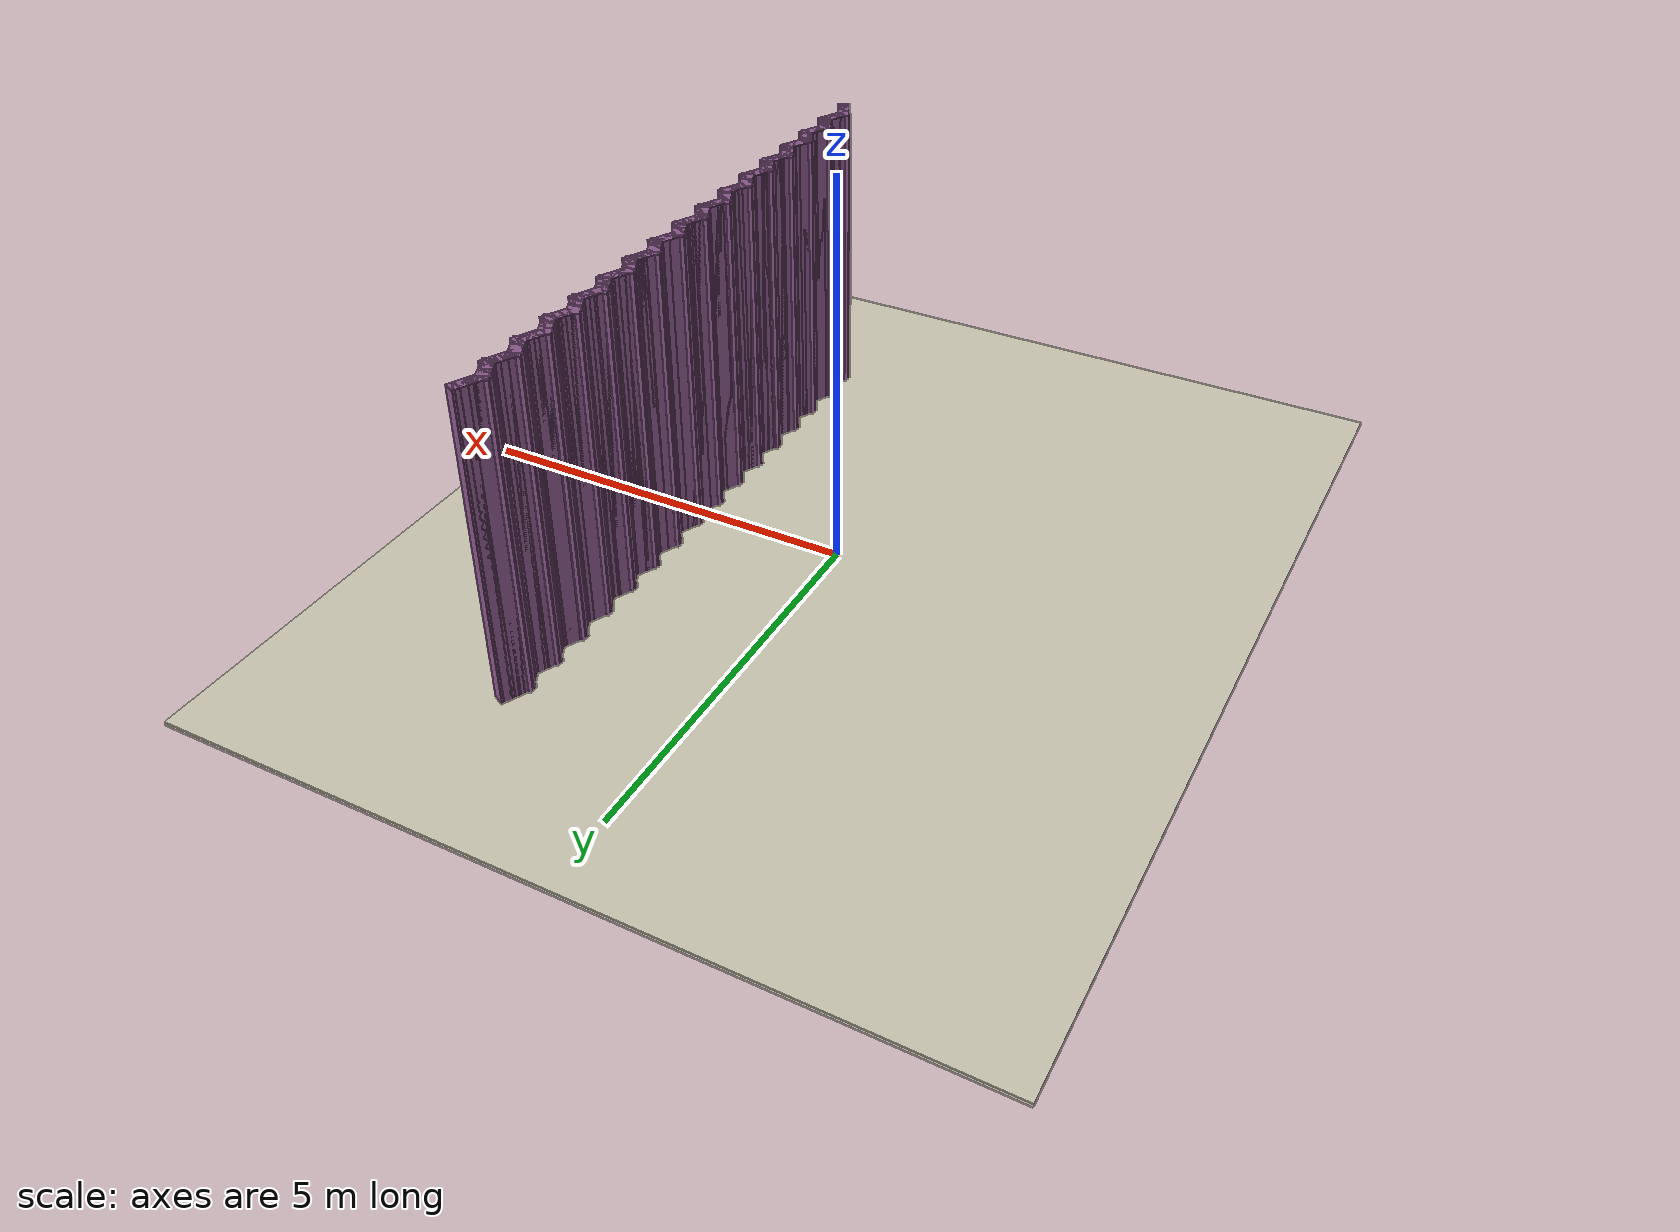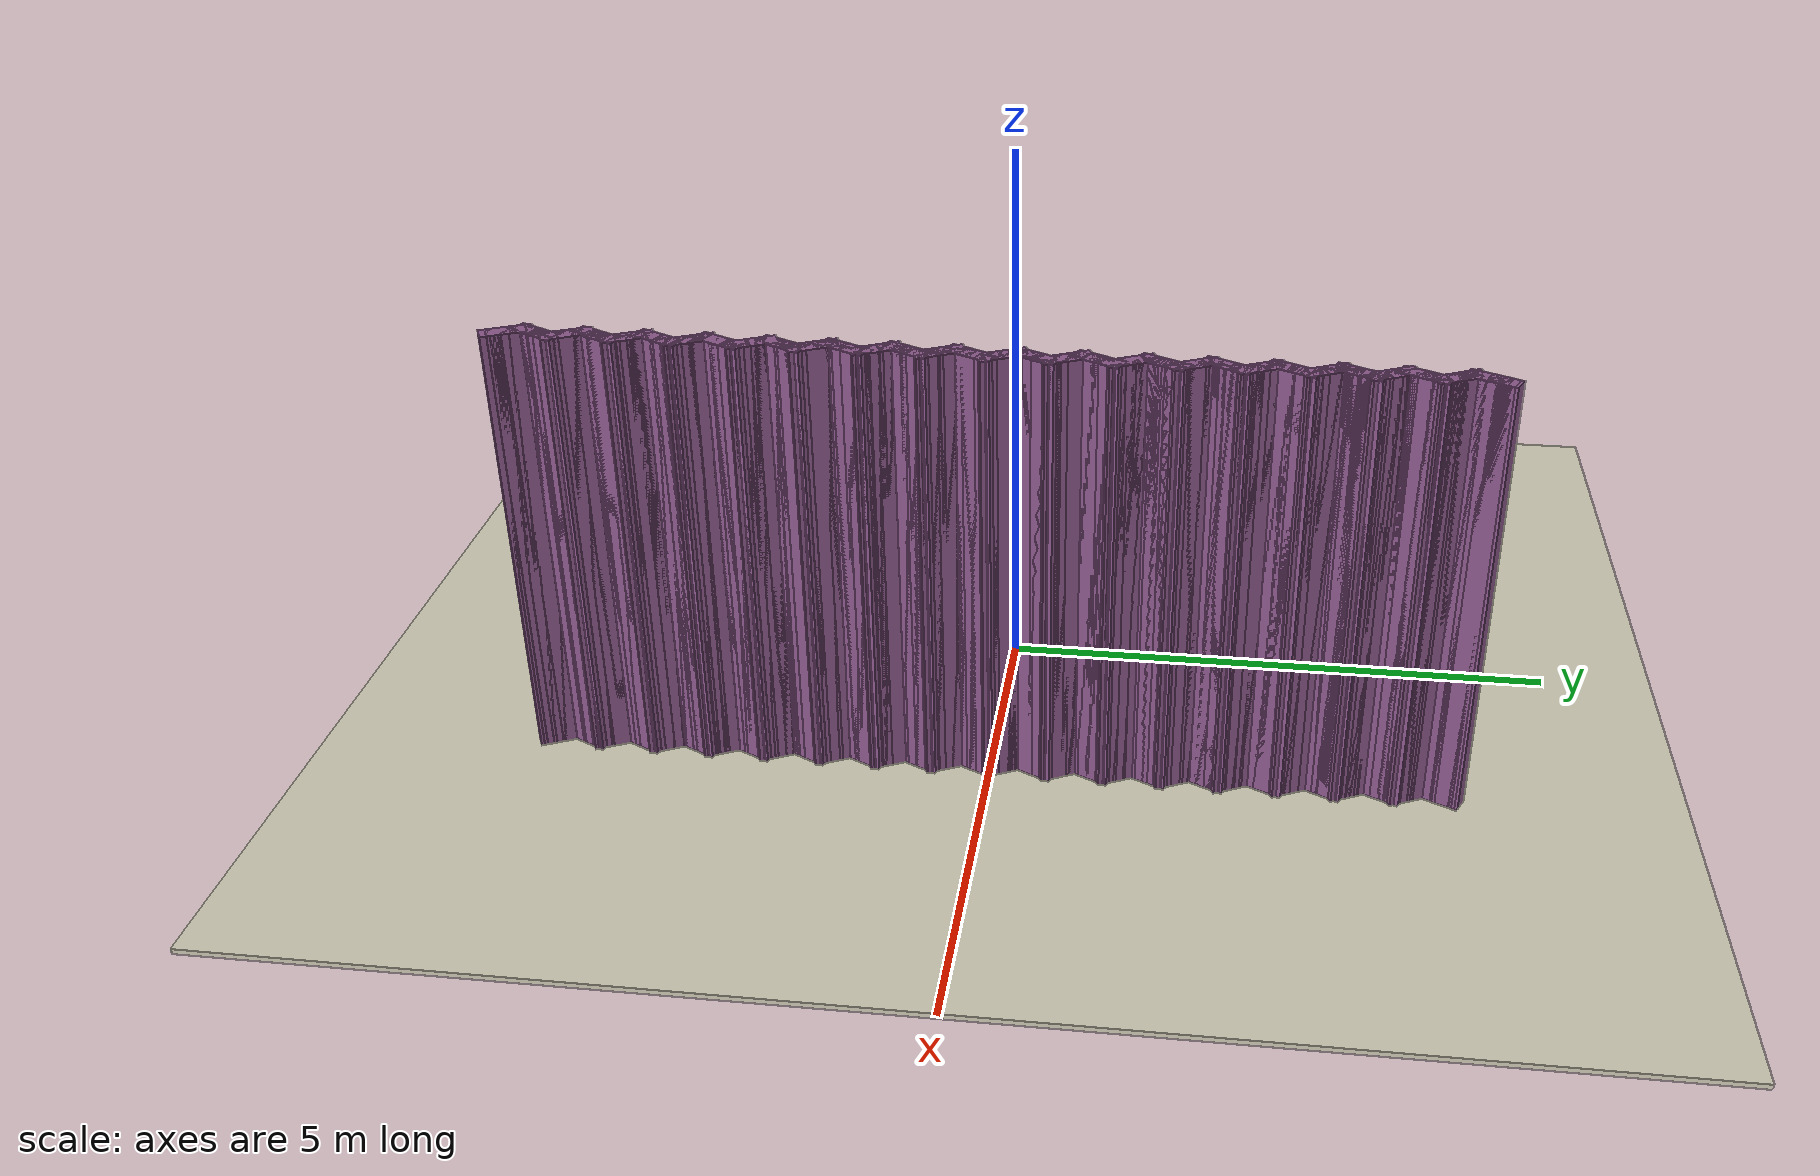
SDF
<sdf version="1.9">
 <world name="p5_serrated">
  <physics name="1ms" type="ignored">
   <max_step_size>0.001</max_step_size>
   <real_time_factor>1.0</real_time_factor>
  </physics>
  <plugin filename="gz-sim-physics-system" name="gz::sim::systems::Physics"/>
  <plugin filename="gz-sim-scene-broadcaster-system" name="gz::sim::systems::SceneBroadcaster"/>
  <plugin filename="gz-sim-user-commands-system" name="gz::sim::systems::UserCommands"/>
  <plugin filename="gz-sim-sensors-system" name="gz::sim::systems::Sensors">
   <render_engine>ogre2</render_engine>
  </plugin>
  <plugin filename="gz-sim-imu-system" name="gz::sim::systems::Imu"/>
  <plugin filename="gz-sim-navsat-system" name="gz::sim::systems::NavSat"/>
  <spherical_coordinates>
   <latitude_deg>-35.363262</latitude_deg>
   <longitude_deg>149.165237</longitude_deg>
   <elevation>584</elevation>
   <heading_deg>0</heading_deg>
   <surface_model>EARTH_WGS84</surface_model>
  </spherical_coordinates>
  <light type="directional" name="main_light">
   <cast_shadows>false</cast_shadows>
   <pose>0 0 10 0 0 0</pose>
   <diffuse>1.0 1.0 1.0 1</diffuse>
   <specular>0.5 0.5 0.5 1</specular>
   <direction>0.1 0.1 -1</direction>
  </light>
  <model name="floor">
   <static>true</static>
   <link name="link">
    <collision name="c"><geometry><box><size>10.0 12.0 0.05</size></box></geometry></collision>
    <visual name="v">
     <geometry><box><size>10.0 12.0 0.05</size></box></geometry>
     <material><ambient>0.82 0.80 0.72 1</ambient><diffuse>0.82 0.80 0.72 1</diffuse></material>
    </visual>
   </link>
  </model>
  <model name="wall_000">
   <static>true</static>
   <pose>1.9940 -3.9875 2.0000 0 0 2.01832</pose>
   <link name="link">
    <collision name="c"><geometry><box><size>0.1777 0.1500 4.0000</size></box></geometry></collision>
    <visual name="v">
     <geometry><box><size>0.1777 0.1500 4.0000</size></box></geometry>
     <material><ambient>0.55 0.35 0.55 1</ambient><diffuse>0.55 0.35 0.55 1</diffuse></material>
    </visual>
   </link>
  </model>
  <model name="wall_001">
   <static>true</static>
   <pose>1.9820 -3.9625 2.0000 0 0 2.01832</pose>
   <link name="link">
    <collision name="c"><geometry><box><size>0.1777 0.1500 4.0000</size></box></geometry></collision>
    <visual name="v">
     <geometry><box><size>0.1777 0.1500 4.0000</size></box></geometry>
     <material><ambient>0.55 0.35 0.55 1</ambient><diffuse>0.55 0.35 0.55 1</diffuse></material>
    </visual>
   </link>
  </model>
  <model name="wall_002">
   <static>true</static>
   <pose>1.9700 -3.9375 2.0000 0 0 2.01832</pose>
   <link name="link">
    <collision name="c"><geometry><box><size>0.1777 0.1500 4.0000</size></box></geometry></collision>
    <visual name="v">
     <geometry><box><size>0.1777 0.1500 4.0000</size></box></geometry>
     <material><ambient>0.55 0.35 0.55 1</ambient><diffuse>0.55 0.35 0.55 1</diffuse></material>
    </visual>
   </link>
  </model>
  <model name="wall_003">
   <static>true</static>
   <pose>1.9580 -3.9125 2.0000 0 0 2.01832</pose>
   <link name="link">
    <collision name="c"><geometry><box><size>0.1777 0.1500 4.0000</size></box></geometry></collision>
    <visual name="v">
     <geometry><box><size>0.1777 0.1500 4.0000</size></box></geometry>
     <material><ambient>0.55 0.35 0.55 1</ambient><diffuse>0.55 0.35 0.55 1</diffuse></material>
    </visual>
   </link>
  </model>
  <model name="wall_004">
   <static>true</static>
   <pose>1.9460 -3.8875 2.0000 0 0 2.01832</pose>
   <link name="link">
    <collision name="c"><geometry><box><size>0.1777 0.1500 4.0000</size></box></geometry></collision>
    <visual name="v">
     <geometry><box><size>0.1777 0.1500 4.0000</size></box></geometry>
     <material><ambient>0.55 0.35 0.55 1</ambient><diffuse>0.55 0.35 0.55 1</diffuse></material>
    </visual>
   </link>
  </model>
  <model name="wall_005">
   <static>true</static>
   <pose>1.9340 -3.8625 2.0000 0 0 2.01832</pose>
   <link name="link">
    <collision name="c"><geometry><box><size>0.1777 0.1500 4.0000</size></box></geometry></collision>
    <visual name="v">
     <geometry><box><size>0.1777 0.1500 4.0000</size></box></geometry>
     <material><ambient>0.55 0.35 0.55 1</ambient><diffuse>0.55 0.35 0.55 1</diffuse></material>
    </visual>
   </link>
  </model>
  <model name="wall_006">
   <static>true</static>
   <pose>1.9220 -3.8375 2.0000 0 0 2.01832</pose>
   <link name="link">
    <collision name="c"><geometry><box><size>0.1777 0.1500 4.0000</size></box></geometry></collision>
    <visual name="v">
     <geometry><box><size>0.1777 0.1500 4.0000</size></box></geometry>
     <material><ambient>0.55 0.35 0.55 1</ambient><diffuse>0.55 0.35 0.55 1</diffuse></material>
    </visual>
   </link>
  </model>
  <model name="wall_007">
   <static>true</static>
   <pose>1.9100 -3.8125 2.0000 0 0 2.01832</pose>
   <link name="link">
    <collision name="c"><geometry><box><size>0.1777 0.1500 4.0000</size></box></geometry></collision>
    <visual name="v">
     <geometry><box><size>0.1777 0.1500 4.0000</size></box></geometry>
     <material><ambient>0.55 0.35 0.55 1</ambient><diffuse>0.55 0.35 0.55 1</diffuse></material>
    </visual>
   </link>
  </model>
  <model name="wall_008">
   <static>true</static>
   <pose>1.8980 -3.7875 2.0000 0 0 2.01832</pose>
   <link name="link">
    <collision name="c"><geometry><box><size>0.1777 0.1500 4.0000</size></box></geometry></collision>
    <visual name="v">
     <geometry><box><size>0.1777 0.1500 4.0000</size></box></geometry>
     <material><ambient>0.55 0.35 0.55 1</ambient><diffuse>0.55 0.35 0.55 1</diffuse></material>
    </visual>
   </link>
  </model>
  <model name="wall_009">
   <static>true</static>
   <pose>1.8860 -3.7625 2.0000 0 0 2.01832</pose>
   <link name="link">
    <collision name="c"><geometry><box><size>0.1777 0.1500 4.0000</size></box></geometry></collision>
    <visual name="v">
     <geometry><box><size>0.1777 0.1500 4.0000</size></box></geometry>
     <material><ambient>0.55 0.35 0.55 1</ambient><diffuse>0.55 0.35 0.55 1</diffuse></material>
    </visual>
   </link>
  </model>
  <model name="wall_010">
   <static>true</static>
   <pose>1.8860 -3.7375 2.0000 0 0 1.12328</pose>
   <link name="link">
    <collision name="c"><geometry><box><size>0.1777 0.1500 4.0000</size></box></geometry></collision>
    <visual name="v">
     <geometry><box><size>0.1777 0.1500 4.0000</size></box></geometry>
     <material><ambient>0.55 0.35 0.55 1</ambient><diffuse>0.55 0.35 0.55 1</diffuse></material>
    </visual>
   </link>
  </model>
  <model name="wall_011">
   <static>true</static>
   <pose>1.8980 -3.7125 2.0000 0 0 1.12328</pose>
   <link name="link">
    <collision name="c"><geometry><box><size>0.1777 0.1500 4.0000</size></box></geometry></collision>
    <visual name="v">
     <geometry><box><size>0.1777 0.1500 4.0000</size></box></geometry>
     <material><ambient>0.55 0.35 0.55 1</ambient><diffuse>0.55 0.35 0.55 1</diffuse></material>
    </visual>
   </link>
  </model>
  <model name="wall_012">
   <static>true</static>
   <pose>1.9100 -3.6875 2.0000 0 0 1.12328</pose>
   <link name="link">
    <collision name="c"><geometry><box><size>0.1777 0.1500 4.0000</size></box></geometry></collision>
    <visual name="v">
     <geometry><box><size>0.1777 0.1500 4.0000</size></box></geometry>
     <material><ambient>0.55 0.35 0.55 1</ambient><diffuse>0.55 0.35 0.55 1</diffuse></material>
    </visual>
   </link>
  </model>
  <model name="wall_013">
   <static>true</static>
   <pose>1.9220 -3.6625 2.0000 0 0 1.12328</pose>
   <link name="link">
    <collision name="c"><geometry><box><size>0.1777 0.1500 4.0000</size></box></geometry></collision>
    <visual name="v">
     <geometry><box><size>0.1777 0.1500 4.0000</size></box></geometry>
     <material><ambient>0.55 0.35 0.55 1</ambient><diffuse>0.55 0.35 0.55 1</diffuse></material>
    </visual>
   </link>
  </model>
  <model name="wall_014">
   <static>true</static>
   <pose>1.9340 -3.6375 2.0000 0 0 1.12328</pose>
   <link name="link">
    <collision name="c"><geometry><box><size>0.1777 0.1500 4.0000</size></box></geometry></collision>
    <visual name="v">
     <geometry><box><size>0.1777 0.1500 4.0000</size></box></geometry>
     <material><ambient>0.55 0.35 0.55 1</ambient><diffuse>0.55 0.35 0.55 1</diffuse></material>
    </visual>
   </link>
  </model>
  <model name="wall_015">
   <static>true</static>
   <pose>1.9460 -3.6125 2.0000 0 0 1.12328</pose>
   <link name="link">
    <collision name="c"><geometry><box><size>0.1777 0.1500 4.0000</size></box></geometry></collision>
    <visual name="v">
     <geometry><box><size>0.1777 0.1500 4.0000</size></box></geometry>
     <material><ambient>0.55 0.35 0.55 1</ambient><diffuse>0.55 0.35 0.55 1</diffuse></material>
    </visual>
   </link>
  </model>
  <model name="wall_016">
   <static>true</static>
   <pose>1.9580 -3.5875 2.0000 0 0 1.12328</pose>
   <link name="link">
    <collision name="c"><geometry><box><size>0.1777 0.1500 4.0000</size></box></geometry></collision>
    <visual name="v">
     <geometry><box><size>0.1777 0.1500 4.0000</size></box></geometry>
     <material><ambient>0.55 0.35 0.55 1</ambient><diffuse>0.55 0.35 0.55 1</diffuse></material>
    </visual>
   </link>
  </model>
  <model name="wall_017">
   <static>true</static>
   <pose>1.9700 -3.5625 2.0000 0 0 1.12328</pose>
   <link name="link">
    <collision name="c"><geometry><box><size>0.1777 0.1500 4.0000</size></box></geometry></collision>
    <visual name="v">
     <geometry><box><size>0.1777 0.1500 4.0000</size></box></geometry>
     <material><ambient>0.55 0.35 0.55 1</ambient><diffuse>0.55 0.35 0.55 1</diffuse></material>
    </visual>
   </link>
  </model>
  <model name="wall_018">
   <static>true</static>
   <pose>1.9820 -3.5375 2.0000 0 0 1.12328</pose>
   <link name="link">
    <collision name="c"><geometry><box><size>0.1777 0.1500 4.0000</size></box></geometry></collision>
    <visual name="v">
     <geometry><box><size>0.1777 0.1500 4.0000</size></box></geometry>
     <material><ambient>0.55 0.35 0.55 1</ambient><diffuse>0.55 0.35 0.55 1</diffuse></material>
    </visual>
   </link>
  </model>
  <model name="wall_019">
   <static>true</static>
   <pose>1.9940 -3.5125 2.0000 0 0 1.12328</pose>
   <link name="link">
    <collision name="c"><geometry><box><size>0.1777 0.1500 4.0000</size></box></geometry></collision>
    <visual name="v">
     <geometry><box><size>0.1777 0.1500 4.0000</size></box></geometry>
     <material><ambient>0.55 0.35 0.55 1</ambient><diffuse>0.55 0.35 0.55 1</diffuse></material>
    </visual>
   </link>
  </model>
  <model name="wall_020">
   <static>true</static>
   <pose>1.9940 -3.4875 2.0000 0 0 2.01832</pose>
   <link name="link">
    <collision name="c"><geometry><box><size>0.1777 0.1500 4.0000</size></box></geometry></collision>
    <visual name="v">
     <geometry><box><size>0.1777 0.1500 4.0000</size></box></geometry>
     <material><ambient>0.55 0.35 0.55 1</ambient><diffuse>0.55 0.35 0.55 1</diffuse></material>
    </visual>
   </link>
  </model>
  <model name="wall_021">
   <static>true</static>
   <pose>1.9820 -3.4625 2.0000 0 0 2.01832</pose>
   <link name="link">
    <collision name="c"><geometry><box><size>0.1777 0.1500 4.0000</size></box></geometry></collision>
    <visual name="v">
     <geometry><box><size>0.1777 0.1500 4.0000</size></box></geometry>
     <material><ambient>0.55 0.35 0.55 1</ambient><diffuse>0.55 0.35 0.55 1</diffuse></material>
    </visual>
   </link>
  </model>
  <model name="wall_022">
   <static>true</static>
   <pose>1.9700 -3.4375 2.0000 0 0 2.01832</pose>
   <link name="link">
    <collision name="c"><geometry><box><size>0.1777 0.1500 4.0000</size></box></geometry></collision>
    <visual name="v">
     <geometry><box><size>0.1777 0.1500 4.0000</size></box></geometry>
     <material><ambient>0.55 0.35 0.55 1</ambient><diffuse>0.55 0.35 0.55 1</diffuse></material>
    </visual>
   </link>
  </model>
  <model name="wall_023">
   <static>true</static>
   <pose>1.9580 -3.4125 2.0000 0 0 2.01832</pose>
   <link name="link">
    <collision name="c"><geometry><box><size>0.1777 0.1500 4.0000</size></box></geometry></collision>
    <visual name="v">
     <geometry><box><size>0.1777 0.1500 4.0000</size></box></geometry>
     <material><ambient>0.55 0.35 0.55 1</ambient><diffuse>0.55 0.35 0.55 1</diffuse></material>
    </visual>
   </link>
  </model>
  <model name="wall_024">
   <static>true</static>
   <pose>1.9460 -3.3875 2.0000 0 0 2.01832</pose>
   <link name="link">
    <collision name="c"><geometry><box><size>0.1777 0.1500 4.0000</size></box></geometry></collision>
    <visual name="v">
     <geometry><box><size>0.1777 0.1500 4.0000</size></box></geometry>
     <material><ambient>0.55 0.35 0.55 1</ambient><diffuse>0.55 0.35 0.55 1</diffuse></material>
    </visual>
   </link>
  </model>
  <model name="wall_025">
   <static>true</static>
   <pose>1.9340 -3.3625 2.0000 0 0 2.01832</pose>
   <link name="link">
    <collision name="c"><geometry><box><size>0.1777 0.1500 4.0000</size></box></geometry></collision>
    <visual name="v">
     <geometry><box><size>0.1777 0.1500 4.0000</size></box></geometry>
     <material><ambient>0.55 0.35 0.55 1</ambient><diffuse>0.55 0.35 0.55 1</diffuse></material>
    </visual>
   </link>
  </model>
  <model name="wall_026">
   <static>true</static>
   <pose>1.9220 -3.3375 2.0000 0 0 2.01832</pose>
   <link name="link">
    <collision name="c"><geometry><box><size>0.1777 0.1500 4.0000</size></box></geometry></collision>
    <visual name="v">
     <geometry><box><size>0.1777 0.1500 4.0000</size></box></geometry>
     <material><ambient>0.55 0.35 0.55 1</ambient><diffuse>0.55 0.35 0.55 1</diffuse></material>
    </visual>
   </link>
  </model>
  <model name="wall_027">
   <static>true</static>
   <pose>1.9100 -3.3125 2.0000 0 0 2.01832</pose>
   <link name="link">
    <collision name="c"><geometry><box><size>0.1777 0.1500 4.0000</size></box></geometry></collision>
    <visual name="v">
     <geometry><box><size>0.1777 0.1500 4.0000</size></box></geometry>
     <material><ambient>0.55 0.35 0.55 1</ambient><diffuse>0.55 0.35 0.55 1</diffuse></material>
    </visual>
   </link>
  </model>
  <model name="wall_028">
   <static>true</static>
   <pose>1.8980 -3.2875 2.0000 0 0 2.01832</pose>
   <link name="link">
    <collision name="c"><geometry><box><size>0.1777 0.1500 4.0000</size></box></geometry></collision>
    <visual name="v">
     <geometry><box><size>0.1777 0.1500 4.0000</size></box></geometry>
     <material><ambient>0.55 0.35 0.55 1</ambient><diffuse>0.55 0.35 0.55 1</diffuse></material>
    </visual>
   </link>
  </model>
  <model name="wall_029">
   <static>true</static>
   <pose>1.8860 -3.2625 2.0000 0 0 2.01832</pose>
   <link name="link">
    <collision name="c"><geometry><box><size>0.1777 0.1500 4.0000</size></box></geometry></collision>
    <visual name="v">
     <geometry><box><size>0.1777 0.1500 4.0000</size></box></geometry>
     <material><ambient>0.55 0.35 0.55 1</ambient><diffuse>0.55 0.35 0.55 1</diffuse></material>
    </visual>
   </link>
  </model>
  <model name="wall_030">
   <static>true</static>
   <pose>1.8860 -3.2375 2.0000 0 0 1.12328</pose>
   <link name="link">
    <collision name="c"><geometry><box><size>0.1777 0.1500 4.0000</size></box></geometry></collision>
    <visual name="v">
     <geometry><box><size>0.1777 0.1500 4.0000</size></box></geometry>
     <material><ambient>0.55 0.35 0.55 1</ambient><diffuse>0.55 0.35 0.55 1</diffuse></material>
    </visual>
   </link>
  </model>
  <model name="wall_031">
   <static>true</static>
   <pose>1.8980 -3.2125 2.0000 0 0 1.12328</pose>
   <link name="link">
    <collision name="c"><geometry><box><size>0.1777 0.1500 4.0000</size></box></geometry></collision>
    <visual name="v">
     <geometry><box><size>0.1777 0.1500 4.0000</size></box></geometry>
     <material><ambient>0.55 0.35 0.55 1</ambient><diffuse>0.55 0.35 0.55 1</diffuse></material>
    </visual>
   </link>
  </model>
  <model name="wall_032">
   <static>true</static>
   <pose>1.9100 -3.1875 2.0000 0 0 1.12328</pose>
   <link name="link">
    <collision name="c"><geometry><box><size>0.1777 0.1500 4.0000</size></box></geometry></collision>
    <visual name="v">
     <geometry><box><size>0.1777 0.1500 4.0000</size></box></geometry>
     <material><ambient>0.55 0.35 0.55 1</ambient><diffuse>0.55 0.35 0.55 1</diffuse></material>
    </visual>
   </link>
  </model>
  <model name="wall_033">
   <static>true</static>
   <pose>1.9220 -3.1625 2.0000 0 0 1.12328</pose>
   <link name="link">
    <collision name="c"><geometry><box><size>0.1777 0.1500 4.0000</size></box></geometry></collision>
    <visual name="v">
     <geometry><box><size>0.1777 0.1500 4.0000</size></box></geometry>
     <material><ambient>0.55 0.35 0.55 1</ambient><diffuse>0.55 0.35 0.55 1</diffuse></material>
    </visual>
   </link>
  </model>
  <model name="wall_034">
   <static>true</static>
   <pose>1.9340 -3.1375 2.0000 0 0 1.12328</pose>
   <link name="link">
    <collision name="c"><geometry><box><size>0.1777 0.1500 4.0000</size></box></geometry></collision>
    <visual name="v">
     <geometry><box><size>0.1777 0.1500 4.0000</size></box></geometry>
     <material><ambient>0.55 0.35 0.55 1</ambient><diffuse>0.55 0.35 0.55 1</diffuse></material>
    </visual>
   </link>
  </model>
  <model name="wall_035">
   <static>true</static>
   <pose>1.9460 -3.1125 2.0000 0 0 1.12328</pose>
   <link name="link">
    <collision name="c"><geometry><box><size>0.1777 0.1500 4.0000</size></box></geometry></collision>
    <visual name="v">
     <geometry><box><size>0.1777 0.1500 4.0000</size></box></geometry>
     <material><ambient>0.55 0.35 0.55 1</ambient><diffuse>0.55 0.35 0.55 1</diffuse></material>
    </visual>
   </link>
  </model>
  <model name="wall_036">
   <static>true</static>
   <pose>1.9580 -3.0875 2.0000 0 0 1.12328</pose>
   <link name="link">
    <collision name="c"><geometry><box><size>0.1777 0.1500 4.0000</size></box></geometry></collision>
    <visual name="v">
     <geometry><box><size>0.1777 0.1500 4.0000</size></box></geometry>
     <material><ambient>0.55 0.35 0.55 1</ambient><diffuse>0.55 0.35 0.55 1</diffuse></material>
    </visual>
   </link>
  </model>
  <model name="wall_037">
   <static>true</static>
   <pose>1.9700 -3.0625 2.0000 0 0 1.12328</pose>
   <link name="link">
    <collision name="c"><geometry><box><size>0.1777 0.1500 4.0000</size></box></geometry></collision>
    <visual name="v">
     <geometry><box><size>0.1777 0.1500 4.0000</size></box></geometry>
     <material><ambient>0.55 0.35 0.55 1</ambient><diffuse>0.55 0.35 0.55 1</diffuse></material>
    </visual>
   </link>
  </model>
  <model name="wall_038">
   <static>true</static>
   <pose>1.9820 -3.0375 2.0000 0 0 1.12328</pose>
   <link name="link">
    <collision name="c"><geometry><box><size>0.1777 0.1500 4.0000</size></box></geometry></collision>
    <visual name="v">
     <geometry><box><size>0.1777 0.1500 4.0000</size></box></geometry>
     <material><ambient>0.55 0.35 0.55 1</ambient><diffuse>0.55 0.35 0.55 1</diffuse></material>
    </visual>
   </link>
  </model>
  <model name="wall_039">
   <static>true</static>
   <pose>1.9940 -3.0125 2.0000 0 0 1.12328</pose>
   <link name="link">
    <collision name="c"><geometry><box><size>0.1777 0.1500 4.0000</size></box></geometry></collision>
    <visual name="v">
     <geometry><box><size>0.1777 0.1500 4.0000</size></box></geometry>
     <material><ambient>0.55 0.35 0.55 1</ambient><diffuse>0.55 0.35 0.55 1</diffuse></material>
    </visual>
   </link>
  </model>
  <model name="wall_040">
   <static>true</static>
   <pose>1.9940 -2.9875 2.0000 0 0 2.01832</pose>
   <link name="link">
    <collision name="c"><geometry><box><size>0.1777 0.1500 4.0000</size></box></geometry></collision>
    <visual name="v">
     <geometry><box><size>0.1777 0.1500 4.0000</size></box></geometry>
     <material><ambient>0.55 0.35 0.55 1</ambient><diffuse>0.55 0.35 0.55 1</diffuse></material>
    </visual>
   </link>
  </model>
  <model name="wall_041">
   <static>true</static>
   <pose>1.9820 -2.9625 2.0000 0 0 2.01832</pose>
   <link name="link">
    <collision name="c"><geometry><box><size>0.1777 0.1500 4.0000</size></box></geometry></collision>
    <visual name="v">
     <geometry><box><size>0.1777 0.1500 4.0000</size></box></geometry>
     <material><ambient>0.55 0.35 0.55 1</ambient><diffuse>0.55 0.35 0.55 1</diffuse></material>
    </visual>
   </link>
  </model>
  <model name="wall_042">
   <static>true</static>
   <pose>1.9700 -2.9375 2.0000 0 0 2.01832</pose>
   <link name="link">
    <collision name="c"><geometry><box><size>0.1777 0.1500 4.0000</size></box></geometry></collision>
    <visual name="v">
     <geometry><box><size>0.1777 0.1500 4.0000</size></box></geometry>
     <material><ambient>0.55 0.35 0.55 1</ambient><diffuse>0.55 0.35 0.55 1</diffuse></material>
    </visual>
   </link>
  </model>
  <model name="wall_043">
   <static>true</static>
   <pose>1.9580 -2.9125 2.0000 0 0 2.01832</pose>
   <link name="link">
    <collision name="c"><geometry><box><size>0.1777 0.1500 4.0000</size></box></geometry></collision>
    <visual name="v">
     <geometry><box><size>0.1777 0.1500 4.0000</size></box></geometry>
     <material><ambient>0.55 0.35 0.55 1</ambient><diffuse>0.55 0.35 0.55 1</diffuse></material>
    </visual>
   </link>
  </model>
  <model name="wall_044">
   <static>true</static>
   <pose>1.9460 -2.8875 2.0000 0 0 2.01832</pose>
   <link name="link">
    <collision name="c"><geometry><box><size>0.1777 0.1500 4.0000</size></box></geometry></collision>
    <visual name="v">
     <geometry><box><size>0.1777 0.1500 4.0000</size></box></geometry>
     <material><ambient>0.55 0.35 0.55 1</ambient><diffuse>0.55 0.35 0.55 1</diffuse></material>
    </visual>
   </link>
  </model>
  <model name="wall_045">
   <static>true</static>
   <pose>1.9340 -2.8625 2.0000 0 0 2.01832</pose>
   <link name="link">
    <collision name="c"><geometry><box><size>0.1777 0.1500 4.0000</size></box></geometry></collision>
    <visual name="v">
     <geometry><box><size>0.1777 0.1500 4.0000</size></box></geometry>
     <material><ambient>0.55 0.35 0.55 1</ambient><diffuse>0.55 0.35 0.55 1</diffuse></material>
    </visual>
   </link>
  </model>
  <model name="wall_046">
   <static>true</static>
   <pose>1.9220 -2.8375 2.0000 0 0 2.01832</pose>
   <link name="link">
    <collision name="c"><geometry><box><size>0.1777 0.1500 4.0000</size></box></geometry></collision>
    <visual name="v">
     <geometry><box><size>0.1777 0.1500 4.0000</size></box></geometry>
     <material><ambient>0.55 0.35 0.55 1</ambient><diffuse>0.55 0.35 0.55 1</diffuse></material>
    </visual>
   </link>
  </model>
  <model name="wall_047">
   <static>true</static>
   <pose>1.9100 -2.8125 2.0000 0 0 2.01832</pose>
   <link name="link">
    <collision name="c"><geometry><box><size>0.1777 0.1500 4.0000</size></box></geometry></collision>
    <visual name="v">
     <geometry><box><size>0.1777 0.1500 4.0000</size></box></geometry>
     <material><ambient>0.55 0.35 0.55 1</ambient><diffuse>0.55 0.35 0.55 1</diffuse></material>
    </visual>
   </link>
  </model>
  <model name="wall_048">
   <static>true</static>
   <pose>1.8980 -2.7875 2.0000 0 0 2.01832</pose>
   <link name="link">
    <collision name="c"><geometry><box><size>0.1777 0.1500 4.0000</size></box></geometry></collision>
    <visual name="v">
     <geometry><box><size>0.1777 0.1500 4.0000</size></box></geometry>
     <material><ambient>0.55 0.35 0.55 1</ambient><diffuse>0.55 0.35 0.55 1</diffuse></material>
    </visual>
   </link>
  </model>
  <model name="wall_049">
   <static>true</static>
   <pose>1.8860 -2.7625 2.0000 0 0 2.01832</pose>
   <link name="link">
    <collision name="c"><geometry><box><size>0.1777 0.1500 4.0000</size></box></geometry></collision>
    <visual name="v">
     <geometry><box><size>0.1777 0.1500 4.0000</size></box></geometry>
     <material><ambient>0.55 0.35 0.55 1</ambient><diffuse>0.55 0.35 0.55 1</diffuse></material>
    </visual>
   </link>
  </model>
  <model name="wall_050">
   <static>true</static>
   <pose>1.8860 -2.7375 2.0000 0 0 1.12328</pose>
   <link name="link">
    <collision name="c"><geometry><box><size>0.1777 0.1500 4.0000</size></box></geometry></collision>
    <visual name="v">
     <geometry><box><size>0.1777 0.1500 4.0000</size></box></geometry>
     <material><ambient>0.55 0.35 0.55 1</ambient><diffuse>0.55 0.35 0.55 1</diffuse></material>
    </visual>
   </link>
  </model>
  <model name="wall_051">
   <static>true</static>
   <pose>1.8980 -2.7125 2.0000 0 0 1.12328</pose>
   <link name="link">
    <collision name="c"><geometry><box><size>0.1777 0.1500 4.0000</size></box></geometry></collision>
    <visual name="v">
     <geometry><box><size>0.1777 0.1500 4.0000</size></box></geometry>
     <material><ambient>0.55 0.35 0.55 1</ambient><diffuse>0.55 0.35 0.55 1</diffuse></material>
    </visual>
   </link>
  </model>
  <model name="wall_052">
   <static>true</static>
   <pose>1.9100 -2.6875 2.0000 0 0 1.12328</pose>
   <link name="link">
    <collision name="c"><geometry><box><size>0.1777 0.1500 4.0000</size></box></geometry></collision>
    <visual name="v">
     <geometry><box><size>0.1777 0.1500 4.0000</size></box></geometry>
     <material><ambient>0.55 0.35 0.55 1</ambient><diffuse>0.55 0.35 0.55 1</diffuse></material>
    </visual>
   </link>
  </model>
  <model name="wall_053">
   <static>true</static>
   <pose>1.9220 -2.6625 2.0000 0 0 1.12328</pose>
   <link name="link">
    <collision name="c"><geometry><box><size>0.1777 0.1500 4.0000</size></box></geometry></collision>
    <visual name="v">
     <geometry><box><size>0.1777 0.1500 4.0000</size></box></geometry>
     <material><ambient>0.55 0.35 0.55 1</ambient><diffuse>0.55 0.35 0.55 1</diffuse></material>
    </visual>
   </link>
  </model>
  <model name="wall_054">
   <static>true</static>
   <pose>1.9340 -2.6375 2.0000 0 0 1.12328</pose>
   <link name="link">
    <collision name="c"><geometry><box><size>0.1777 0.1500 4.0000</size></box></geometry></collision>
    <visual name="v">
     <geometry><box><size>0.1777 0.1500 4.0000</size></box></geometry>
     <material><ambient>0.55 0.35 0.55 1</ambient><diffuse>0.55 0.35 0.55 1</diffuse></material>
    </visual>
   </link>
  </model>
  <model name="wall_055">
   <static>true</static>
   <pose>1.9460 -2.6125 2.0000 0 0 1.12328</pose>
   <link name="link">
    <collision name="c"><geometry><box><size>0.1777 0.1500 4.0000</size></box></geometry></collision>
    <visual name="v">
     <geometry><box><size>0.1777 0.1500 4.0000</size></box></geometry>
     <material><ambient>0.55 0.35 0.55 1</ambient><diffuse>0.55 0.35 0.55 1</diffuse></material>
    </visual>
   </link>
  </model>
  <model name="wall_056">
   <static>true</static>
   <pose>1.9580 -2.5875 2.0000 0 0 1.12328</pose>
   <link name="link">
    <collision name="c"><geometry><box><size>0.1777 0.1500 4.0000</size></box></geometry></collision>
    <visual name="v">
     <geometry><box><size>0.1777 0.1500 4.0000</size></box></geometry>
     <material><ambient>0.55 0.35 0.55 1</ambient><diffuse>0.55 0.35 0.55 1</diffuse></material>
    </visual>
   </link>
  </model>
  <model name="wall_057">
   <static>true</static>
   <pose>1.9700 -2.5625 2.0000 0 0 1.12328</pose>
   <link name="link">
    <collision name="c"><geometry><box><size>0.1777 0.1500 4.0000</size></box></geometry></collision>
    <visual name="v">
     <geometry><box><size>0.1777 0.1500 4.0000</size></box></geometry>
     <material><ambient>0.55 0.35 0.55 1</ambient><diffuse>0.55 0.35 0.55 1</diffuse></material>
    </visual>
   </link>
  </model>
  <model name="wall_058">
   <static>true</static>
   <pose>1.9820 -2.5375 2.0000 0 0 1.12328</pose>
   <link name="link">
    <collision name="c"><geometry><box><size>0.1777 0.1500 4.0000</size></box></geometry></collision>
    <visual name="v">
     <geometry><box><size>0.1777 0.1500 4.0000</size></box></geometry>
     <material><ambient>0.55 0.35 0.55 1</ambient><diffuse>0.55 0.35 0.55 1</diffuse></material>
    </visual>
   </link>
  </model>
  <model name="wall_059">
   <static>true</static>
   <pose>1.9940 -2.5125 2.0000 0 0 1.12328</pose>
   <link name="link">
    <collision name="c"><geometry><box><size>0.1777 0.1500 4.0000</size></box></geometry></collision>
    <visual name="v">
     <geometry><box><size>0.1777 0.1500 4.0000</size></box></geometry>
     <material><ambient>0.55 0.35 0.55 1</ambient><diffuse>0.55 0.35 0.55 1</diffuse></material>
    </visual>
   </link>
  </model>
  <model name="wall_060">
   <static>true</static>
   <pose>1.9940 -2.4875 2.0000 0 0 2.01832</pose>
   <link name="link">
    <collision name="c"><geometry><box><size>0.1777 0.1500 4.0000</size></box></geometry></collision>
    <visual name="v">
     <geometry><box><size>0.1777 0.1500 4.0000</size></box></geometry>
     <material><ambient>0.55 0.35 0.55 1</ambient><diffuse>0.55 0.35 0.55 1</diffuse></material>
    </visual>
   </link>
  </model>
  <model name="wall_061">
   <static>true</static>
   <pose>1.9820 -2.4625 2.0000 0 0 2.01832</pose>
   <link name="link">
    <collision name="c"><geometry><box><size>0.1777 0.1500 4.0000</size></box></geometry></collision>
    <visual name="v">
     <geometry><box><size>0.1777 0.1500 4.0000</size></box></geometry>
     <material><ambient>0.55 0.35 0.55 1</ambient><diffuse>0.55 0.35 0.55 1</diffuse></material>
    </visual>
   </link>
  </model>
  <model name="wall_062">
   <static>true</static>
   <pose>1.9700 -2.4375 2.0000 0 0 2.01832</pose>
   <link name="link">
    <collision name="c"><geometry><box><size>0.1777 0.1500 4.0000</size></box></geometry></collision>
    <visual name="v">
     <geometry><box><size>0.1777 0.1500 4.0000</size></box></geometry>
     <material><ambient>0.55 0.35 0.55 1</ambient><diffuse>0.55 0.35 0.55 1</diffuse></material>
    </visual>
   </link>
  </model>
  <model name="wall_063">
   <static>true</static>
   <pose>1.9580 -2.4125 2.0000 0 0 2.01832</pose>
   <link name="link">
    <collision name="c"><geometry><box><size>0.1777 0.1500 4.0000</size></box></geometry></collision>
    <visual name="v">
     <geometry><box><size>0.1777 0.1500 4.0000</size></box></geometry>
     <material><ambient>0.55 0.35 0.55 1</ambient><diffuse>0.55 0.35 0.55 1</diffuse></material>
    </visual>
   </link>
  </model>
  <model name="wall_064">
   <static>true</static>
   <pose>1.9460 -2.3875 2.0000 0 0 2.01832</pose>
   <link name="link">
    <collision name="c"><geometry><box><size>0.1777 0.1500 4.0000</size></box></geometry></collision>
    <visual name="v">
     <geometry><box><size>0.1777 0.1500 4.0000</size></box></geometry>
     <material><ambient>0.55 0.35 0.55 1</ambient><diffuse>0.55 0.35 0.55 1</diffuse></material>
    </visual>
   </link>
  </model>
  <model name="wall_065">
   <static>true</static>
   <pose>1.9340 -2.3625 2.0000 0 0 2.01832</pose>
   <link name="link">
    <collision name="c"><geometry><box><size>0.1777 0.1500 4.0000</size></box></geometry></collision>
    <visual name="v">
     <geometry><box><size>0.1777 0.1500 4.0000</size></box></geometry>
     <material><ambient>0.55 0.35 0.55 1</ambient><diffuse>0.55 0.35 0.55 1</diffuse></material>
    </visual>
   </link>
  </model>
  <model name="wall_066">
   <static>true</static>
   <pose>1.9220 -2.3375 2.0000 0 0 2.01832</pose>
   <link name="link">
    <collision name="c"><geometry><box><size>0.1777 0.1500 4.0000</size></box></geometry></collision>
    <visual name="v">
     <geometry><box><size>0.1777 0.1500 4.0000</size></box></geometry>
     <material><ambient>0.55 0.35 0.55 1</ambient><diffuse>0.55 0.35 0.55 1</diffuse></material>
    </visual>
   </link>
  </model>
  <model name="wall_067">
   <static>true</static>
   <pose>1.9100 -2.3125 2.0000 0 0 2.01832</pose>
   <link name="link">
    <collision name="c"><geometry><box><size>0.1777 0.1500 4.0000</size></box></geometry></collision>
    <visual name="v">
     <geometry><box><size>0.1777 0.1500 4.0000</size></box></geometry>
     <material><ambient>0.55 0.35 0.55 1</ambient><diffuse>0.55 0.35 0.55 1</diffuse></material>
    </visual>
   </link>
  </model>
  <model name="wall_068">
   <static>true</static>
   <pose>1.8980 -2.2875 2.0000 0 0 2.01832</pose>
   <link name="link">
    <collision name="c"><geometry><box><size>0.1777 0.1500 4.0000</size></box></geometry></collision>
    <visual name="v">
     <geometry><box><size>0.1777 0.1500 4.0000</size></box></geometry>
     <material><ambient>0.55 0.35 0.55 1</ambient><diffuse>0.55 0.35 0.55 1</diffuse></material>
    </visual>
   </link>
  </model>
  <model name="wall_069">
   <static>true</static>
   <pose>1.8860 -2.2625 2.0000 0 0 2.01832</pose>
   <link name="link">
    <collision name="c"><geometry><box><size>0.1777 0.1500 4.0000</size></box></geometry></collision>
    <visual name="v">
     <geometry><box><size>0.1777 0.1500 4.0000</size></box></geometry>
     <material><ambient>0.55 0.35 0.55 1</ambient><diffuse>0.55 0.35 0.55 1</diffuse></material>
    </visual>
   </link>
  </model>
  <model name="wall_070">
   <static>true</static>
   <pose>1.8860 -2.2375 2.0000 0 0 1.12328</pose>
   <link name="link">
    <collision name="c"><geometry><box><size>0.1777 0.1500 4.0000</size></box></geometry></collision>
    <visual name="v">
     <geometry><box><size>0.1777 0.1500 4.0000</size></box></geometry>
     <material><ambient>0.55 0.35 0.55 1</ambient><diffuse>0.55 0.35 0.55 1</diffuse></material>
    </visual>
   </link>
  </model>
  <model name="wall_071">
   <static>true</static>
   <pose>1.8980 -2.2125 2.0000 0 0 1.12328</pose>
   <link name="link">
    <collision name="c"><geometry><box><size>0.1777 0.1500 4.0000</size></box></geometry></collision>
    <visual name="v">
     <geometry><box><size>0.1777 0.1500 4.0000</size></box></geometry>
     <material><ambient>0.55 0.35 0.55 1</ambient><diffuse>0.55 0.35 0.55 1</diffuse></material>
    </visual>
   </link>
  </model>
  <model name="wall_072">
   <static>true</static>
   <pose>1.9100 -2.1875 2.0000 0 0 1.12328</pose>
   <link name="link">
    <collision name="c"><geometry><box><size>0.1777 0.1500 4.0000</size></box></geometry></collision>
    <visual name="v">
     <geometry><box><size>0.1777 0.1500 4.0000</size></box></geometry>
     <material><ambient>0.55 0.35 0.55 1</ambient><diffuse>0.55 0.35 0.55 1</diffuse></material>
    </visual>
   </link>
  </model>
  <model name="wall_073">
   <static>true</static>
   <pose>1.9220 -2.1625 2.0000 0 0 1.12328</pose>
   <link name="link">
    <collision name="c"><geometry><box><size>0.1777 0.1500 4.0000</size></box></geometry></collision>
    <visual name="v">
     <geometry><box><size>0.1777 0.1500 4.0000</size></box></geometry>
     <material><ambient>0.55 0.35 0.55 1</ambient><diffuse>0.55 0.35 0.55 1</diffuse></material>
    </visual>
   </link>
  </model>
  <model name="wall_074">
   <static>true</static>
   <pose>1.9340 -2.1375 2.0000 0 0 1.12328</pose>
   <link name="link">
    <collision name="c"><geometry><box><size>0.1777 0.1500 4.0000</size></box></geometry></collision>
    <visual name="v">
     <geometry><box><size>0.1777 0.1500 4.0000</size></box></geometry>
     <material><ambient>0.55 0.35 0.55 1</ambient><diffuse>0.55 0.35 0.55 1</diffuse></material>
    </visual>
   </link>
  </model>
  <model name="wall_075">
   <static>true</static>
   <pose>1.9460 -2.1125 2.0000 0 0 1.12328</pose>
   <link name="link">
    <collision name="c"><geometry><box><size>0.1777 0.1500 4.0000</size></box></geometry></collision>
    <visual name="v">
     <geometry><box><size>0.1777 0.1500 4.0000</size></box></geometry>
     <material><ambient>0.55 0.35 0.55 1</ambient><diffuse>0.55 0.35 0.55 1</diffuse></material>
    </visual>
   </link>
  </model>
  <model name="wall_076">
   <static>true</static>
   <pose>1.9580 -2.0875 2.0000 0 0 1.12328</pose>
   <link name="link">
    <collision name="c"><geometry><box><size>0.1777 0.1500 4.0000</size></box></geometry></collision>
    <visual name="v">
     <geometry><box><size>0.1777 0.1500 4.0000</size></box></geometry>
     <material><ambient>0.55 0.35 0.55 1</ambient><diffuse>0.55 0.35 0.55 1</diffuse></material>
    </visual>
   </link>
  </model>
  <model name="wall_077">
   <static>true</static>
   <pose>1.9700 -2.0625 2.0000 0 0 1.12328</pose>
   <link name="link">
    <collision name="c"><geometry><box><size>0.1777 0.1500 4.0000</size></box></geometry></collision>
    <visual name="v">
     <geometry><box><size>0.1777 0.1500 4.0000</size></box></geometry>
     <material><ambient>0.55 0.35 0.55 1</ambient><diffuse>0.55 0.35 0.55 1</diffuse></material>
    </visual>
   </link>
  </model>
  <model name="wall_078">
   <static>true</static>
   <pose>1.9820 -2.0375 2.0000 0 0 1.12328</pose>
   <link name="link">
    <collision name="c"><geometry><box><size>0.1777 0.1500 4.0000</size></box></geometry></collision>
    <visual name="v">
     <geometry><box><size>0.1777 0.1500 4.0000</size></box></geometry>
     <material><ambient>0.55 0.35 0.55 1</ambient><diffuse>0.55 0.35 0.55 1</diffuse></material>
    </visual>
   </link>
  </model>
  <model name="wall_079">
   <static>true</static>
   <pose>1.9940 -2.0125 2.0000 0 0 1.12328</pose>
   <link name="link">
    <collision name="c"><geometry><box><size>0.1777 0.1500 4.0000</size></box></geometry></collision>
    <visual name="v">
     <geometry><box><size>0.1777 0.1500 4.0000</size></box></geometry>
     <material><ambient>0.55 0.35 0.55 1</ambient><diffuse>0.55 0.35 0.55 1</diffuse></material>
    </visual>
   </link>
  </model>
  <model name="wall_080">
   <static>true</static>
   <pose>1.9940 -1.9875 2.0000 0 0 2.01832</pose>
   <link name="link">
    <collision name="c"><geometry><box><size>0.1777 0.1500 4.0000</size></box></geometry></collision>
    <visual name="v">
     <geometry><box><size>0.1777 0.1500 4.0000</size></box></geometry>
     <material><ambient>0.55 0.35 0.55 1</ambient><diffuse>0.55 0.35 0.55 1</diffuse></material>
    </visual>
   </link>
  </model>
  <model name="wall_081">
   <static>true</static>
   <pose>1.9820 -1.9625 2.0000 0 0 2.01832</pose>
   <link name="link">
    <collision name="c"><geometry><box><size>0.1777 0.1500 4.0000</size></box></geometry></collision>
    <visual name="v">
     <geometry><box><size>0.1777 0.1500 4.0000</size></box></geometry>
     <material><ambient>0.55 0.35 0.55 1</ambient><diffuse>0.55 0.35 0.55 1</diffuse></material>
    </visual>
   </link>
  </model>
  <model name="wall_082">
   <static>true</static>
   <pose>1.9700 -1.9375 2.0000 0 0 2.01832</pose>
   <link name="link">
    <collision name="c"><geometry><box><size>0.1777 0.1500 4.0000</size></box></geometry></collision>
    <visual name="v">
     <geometry><box><size>0.1777 0.1500 4.0000</size></box></geometry>
     <material><ambient>0.55 0.35 0.55 1</ambient><diffuse>0.55 0.35 0.55 1</diffuse></material>
    </visual>
   </link>
  </model>
  <model name="wall_083">
   <static>true</static>
   <pose>1.9580 -1.9125 2.0000 0 0 2.01832</pose>
   <link name="link">
    <collision name="c"><geometry><box><size>0.1777 0.1500 4.0000</size></box></geometry></collision>
    <visual name="v">
     <geometry><box><size>0.1777 0.1500 4.0000</size></box></geometry>
     <material><ambient>0.55 0.35 0.55 1</ambient><diffuse>0.55 0.35 0.55 1</diffuse></material>
    </visual>
   </link>
  </model>
  <model name="wall_084">
   <static>true</static>
   <pose>1.9460 -1.8875 2.0000 0 0 2.01832</pose>
   <link name="link">
    <collision name="c"><geometry><box><size>0.1777 0.1500 4.0000</size></box></geometry></collision>
    <visual name="v">
     <geometry><box><size>0.1777 0.1500 4.0000</size></box></geometry>
     <material><ambient>0.55 0.35 0.55 1</ambient><diffuse>0.55 0.35 0.55 1</diffuse></material>
    </visual>
   </link>
  </model>
  <model name="wall_085">
   <static>true</static>
   <pose>1.9340 -1.8625 2.0000 0 0 2.01832</pose>
   <link name="link">
    <collision name="c"><geometry><box><size>0.1777 0.1500 4.0000</size></box></geometry></collision>
    <visual name="v">
     <geometry><box><size>0.1777 0.1500 4.0000</size></box></geometry>
     <material><ambient>0.55 0.35 0.55 1</ambient><diffuse>0.55 0.35 0.55 1</diffuse></material>
    </visual>
   </link>
  </model>
  <model name="wall_086">
   <static>true</static>
   <pose>1.9220 -1.8375 2.0000 0 0 2.01832</pose>
   <link name="link">
    <collision name="c"><geometry><box><size>0.1777 0.1500 4.0000</size></box></geometry></collision>
    <visual name="v">
     <geometry><box><size>0.1777 0.1500 4.0000</size></box></geometry>
     <material><ambient>0.55 0.35 0.55 1</ambient><diffuse>0.55 0.35 0.55 1</diffuse></material>
    </visual>
   </link>
  </model>
  <model name="wall_087">
   <static>true</static>
   <pose>1.9100 -1.8125 2.0000 0 0 2.01832</pose>
   <link name="link">
    <collision name="c"><geometry><box><size>0.1777 0.1500 4.0000</size></box></geometry></collision>
    <visual name="v">
     <geometry><box><size>0.1777 0.1500 4.0000</size></box></geometry>
     <material><ambient>0.55 0.35 0.55 1</ambient><diffuse>0.55 0.35 0.55 1</diffuse></material>
    </visual>
   </link>
  </model>
  <model name="wall_088">
   <static>true</static>
   <pose>1.8980 -1.7875 2.0000 0 0 2.01832</pose>
   <link name="link">
    <collision name="c"><geometry><box><size>0.1777 0.1500 4.0000</size></box></geometry></collision>
    <visual name="v">
     <geometry><box><size>0.1777 0.1500 4.0000</size></box></geometry>
     <material><ambient>0.55 0.35 0.55 1</ambient><diffuse>0.55 0.35 0.55 1</diffuse></material>
    </visual>
   </link>
  </model>
  <model name="wall_089">
   <static>true</static>
   <pose>1.8860 -1.7625 2.0000 0 0 2.01832</pose>
   <link name="link">
    <collision name="c"><geometry><box><size>0.1777 0.1500 4.0000</size></box></geometry></collision>
    <visual name="v">
     <geometry><box><size>0.1777 0.1500 4.0000</size></box></geometry>
     <material><ambient>0.55 0.35 0.55 1</ambient><diffuse>0.55 0.35 0.55 1</diffuse></material>
    </visual>
   </link>
  </model>
  <model name="wall_090">
   <static>true</static>
   <pose>1.8860 -1.7375 2.0000 0 0 1.12328</pose>
   <link name="link">
    <collision name="c"><geometry><box><size>0.1777 0.1500 4.0000</size></box></geometry></collision>
    <visual name="v">
     <geometry><box><size>0.1777 0.1500 4.0000</size></box></geometry>
     <material><ambient>0.55 0.35 0.55 1</ambient><diffuse>0.55 0.35 0.55 1</diffuse></material>
    </visual>
   </link>
  </model>
  <model name="wall_091">
   <static>true</static>
   <pose>1.8980 -1.7125 2.0000 0 0 1.12328</pose>
   <link name="link">
    <collision name="c"><geometry><box><size>0.1777 0.1500 4.0000</size></box></geometry></collision>
    <visual name="v">
     <geometry><box><size>0.1777 0.1500 4.0000</size></box></geometry>
     <material><ambient>0.55 0.35 0.55 1</ambient><diffuse>0.55 0.35 0.55 1</diffuse></material>
    </visual>
   </link>
  </model>
  <model name="wall_092">
   <static>true</static>
   <pose>1.9100 -1.6875 2.0000 0 0 1.12328</pose>
   <link name="link">
    <collision name="c"><geometry><box><size>0.1777 0.1500 4.0000</size></box></geometry></collision>
    <visual name="v">
     <geometry><box><size>0.1777 0.1500 4.0000</size></box></geometry>
     <material><ambient>0.55 0.35 0.55 1</ambient><diffuse>0.55 0.35 0.55 1</diffuse></material>
    </visual>
   </link>
  </model>
  <model name="wall_093">
   <static>true</static>
   <pose>1.9220 -1.6625 2.0000 0 0 1.12328</pose>
   <link name="link">
    <collision name="c"><geometry><box><size>0.1777 0.1500 4.0000</size></box></geometry></collision>
    <visual name="v">
     <geometry><box><size>0.1777 0.1500 4.0000</size></box></geometry>
     <material><ambient>0.55 0.35 0.55 1</ambient><diffuse>0.55 0.35 0.55 1</diffuse></material>
    </visual>
   </link>
  </model>
  <model name="wall_094">
   <static>true</static>
   <pose>1.9340 -1.6375 2.0000 0 0 1.12328</pose>
   <link name="link">
    <collision name="c"><geometry><box><size>0.1777 0.1500 4.0000</size></box></geometry></collision>
    <visual name="v">
     <geometry><box><size>0.1777 0.1500 4.0000</size></box></geometry>
     <material><ambient>0.55 0.35 0.55 1</ambient><diffuse>0.55 0.35 0.55 1</diffuse></material>
    </visual>
   </link>
  </model>
  <model name="wall_095">
   <static>true</static>
   <pose>1.9460 -1.6125 2.0000 0 0 1.12328</pose>
   <link name="link">
    <collision name="c"><geometry><box><size>0.1777 0.1500 4.0000</size></box></geometry></collision>
    <visual name="v">
     <geometry><box><size>0.1777 0.1500 4.0000</size></box></geometry>
     <material><ambient>0.55 0.35 0.55 1</ambient><diffuse>0.55 0.35 0.55 1</diffuse></material>
    </visual>
   </link>
  </model>
  <model name="wall_096">
   <static>true</static>
   <pose>1.9580 -1.5875 2.0000 0 0 1.12328</pose>
   <link name="link">
    <collision name="c"><geometry><box><size>0.1777 0.1500 4.0000</size></box></geometry></collision>
    <visual name="v">
     <geometry><box><size>0.1777 0.1500 4.0000</size></box></geometry>
     <material><ambient>0.55 0.35 0.55 1</ambient><diffuse>0.55 0.35 0.55 1</diffuse></material>
    </visual>
   </link>
  </model>
  <model name="wall_097">
   <static>true</static>
   <pose>1.9700 -1.5625 2.0000 0 0 1.12328</pose>
   <link name="link">
    <collision name="c"><geometry><box><size>0.1777 0.1500 4.0000</size></box></geometry></collision>
    <visual name="v">
     <geometry><box><size>0.1777 0.1500 4.0000</size></box></geometry>
     <material><ambient>0.55 0.35 0.55 1</ambient><diffuse>0.55 0.35 0.55 1</diffuse></material>
    </visual>
   </link>
  </model>
  <model name="wall_098">
   <static>true</static>
   <pose>1.9820 -1.5375 2.0000 0 0 1.12328</pose>
   <link name="link">
    <collision name="c"><geometry><box><size>0.1777 0.1500 4.0000</size></box></geometry></collision>
    <visual name="v">
     <geometry><box><size>0.1777 0.1500 4.0000</size></box></geometry>
     <material><ambient>0.55 0.35 0.55 1</ambient><diffuse>0.55 0.35 0.55 1</diffuse></material>
    </visual>
   </link>
  </model>
  <model name="wall_099">
   <static>true</static>
   <pose>1.9940 -1.5125 2.0000 0 0 1.12328</pose>
   <link name="link">
    <collision name="c"><geometry><box><size>0.1777 0.1500 4.0000</size></box></geometry></collision>
    <visual name="v">
     <geometry><box><size>0.1777 0.1500 4.0000</size></box></geometry>
     <material><ambient>0.55 0.35 0.55 1</ambient><diffuse>0.55 0.35 0.55 1</diffuse></material>
    </visual>
   </link>
  </model>
  <model name="wall_100">
   <static>true</static>
   <pose>1.9940 -1.4875 2.0000 0 0 2.01832</pose>
   <link name="link">
    <collision name="c"><geometry><box><size>0.1777 0.1500 4.0000</size></box></geometry></collision>
    <visual name="v">
     <geometry><box><size>0.1777 0.1500 4.0000</size></box></geometry>
     <material><ambient>0.55 0.35 0.55 1</ambient><diffuse>0.55 0.35 0.55 1</diffuse></material>
    </visual>
   </link>
  </model>
  <model name="wall_101">
   <static>true</static>
   <pose>1.9820 -1.4625 2.0000 0 0 2.01832</pose>
   <link name="link">
    <collision name="c"><geometry><box><size>0.1777 0.1500 4.0000</size></box></geometry></collision>
    <visual name="v">
     <geometry><box><size>0.1777 0.1500 4.0000</size></box></geometry>
     <material><ambient>0.55 0.35 0.55 1</ambient><diffuse>0.55 0.35 0.55 1</diffuse></material>
    </visual>
   </link>
  </model>
  <model name="wall_102">
   <static>true</static>
   <pose>1.9700 -1.4375 2.0000 0 0 2.01832</pose>
   <link name="link">
    <collision name="c"><geometry><box><size>0.1777 0.1500 4.0000</size></box></geometry></collision>
    <visual name="v">
     <geometry><box><size>0.1777 0.1500 4.0000</size></box></geometry>
     <material><ambient>0.55 0.35 0.55 1</ambient><diffuse>0.55 0.35 0.55 1</diffuse></material>
    </visual>
   </link>
  </model>
  <model name="wall_103">
   <static>true</static>
   <pose>1.9580 -1.4125 2.0000 0 0 2.01832</pose>
   <link name="link">
    <collision name="c"><geometry><box><size>0.1777 0.1500 4.0000</size></box></geometry></collision>
    <visual name="v">
     <geometry><box><size>0.1777 0.1500 4.0000</size></box></geometry>
     <material><ambient>0.55 0.35 0.55 1</ambient><diffuse>0.55 0.35 0.55 1</diffuse></material>
    </visual>
   </link>
  </model>
  <model name="wall_104">
   <static>true</static>
   <pose>1.9460 -1.3875 2.0000 0 0 2.01832</pose>
   <link name="link">
    <collision name="c"><geometry><box><size>0.1777 0.1500 4.0000</size></box></geometry></collision>
    <visual name="v">
     <geometry><box><size>0.1777 0.1500 4.0000</size></box></geometry>
     <material><ambient>0.55 0.35 0.55 1</ambient><diffuse>0.55 0.35 0.55 1</diffuse></material>
    </visual>
   </link>
  </model>
  <model name="wall_105">
   <static>true</static>
   <pose>1.9340 -1.3625 2.0000 0 0 2.01832</pose>
   <link name="link">
    <collision name="c"><geometry><box><size>0.1777 0.1500 4.0000</size></box></geometry></collision>
    <visual name="v">
     <geometry><box><size>0.1777 0.1500 4.0000</size></box></geometry>
     <material><ambient>0.55 0.35 0.55 1</ambient><diffuse>0.55 0.35 0.55 1</diffuse></material>
    </visual>
   </link>
  </model>
  <model name="wall_106">
   <static>true</static>
   <pose>1.9220 -1.3375 2.0000 0 0 2.01832</pose>
   <link name="link">
    <collision name="c"><geometry><box><size>0.1777 0.1500 4.0000</size></box></geometry></collision>
    <visual name="v">
     <geometry><box><size>0.1777 0.1500 4.0000</size></box></geometry>
     <material><ambient>0.55 0.35 0.55 1</ambient><diffuse>0.55 0.35 0.55 1</diffuse></material>
    </visual>
   </link>
  </model>
  <model name="wall_107">
   <static>true</static>
   <pose>1.9100 -1.3125 2.0000 0 0 2.01832</pose>
   <link name="link">
    <collision name="c"><geometry><box><size>0.1777 0.1500 4.0000</size></box></geometry></collision>
    <visual name="v">
     <geometry><box><size>0.1777 0.1500 4.0000</size></box></geometry>
     <material><ambient>0.55 0.35 0.55 1</ambient><diffuse>0.55 0.35 0.55 1</diffuse></material>
    </visual>
   </link>
  </model>
  <model name="wall_108">
   <static>true</static>
   <pose>1.8980 -1.2875 2.0000 0 0 2.01832</pose>
   <link name="link">
    <collision name="c"><geometry><box><size>0.1777 0.1500 4.0000</size></box></geometry></collision>
    <visual name="v">
     <geometry><box><size>0.1777 0.1500 4.0000</size></box></geometry>
     <material><ambient>0.55 0.35 0.55 1</ambient><diffuse>0.55 0.35 0.55 1</diffuse></material>
    </visual>
   </link>
  </model>
  <model name="wall_109">
   <static>true</static>
   <pose>1.8860 -1.2625 2.0000 0 0 2.01832</pose>
   <link name="link">
    <collision name="c"><geometry><box><size>0.1777 0.1500 4.0000</size></box></geometry></collision>
    <visual name="v">
     <geometry><box><size>0.1777 0.1500 4.0000</size></box></geometry>
     <material><ambient>0.55 0.35 0.55 1</ambient><diffuse>0.55 0.35 0.55 1</diffuse></material>
    </visual>
   </link>
  </model>
  <model name="wall_110">
   <static>true</static>
   <pose>1.8860 -1.2375 2.0000 0 0 1.12328</pose>
   <link name="link">
    <collision name="c"><geometry><box><size>0.1777 0.1500 4.0000</size></box></geometry></collision>
    <visual name="v">
     <geometry><box><size>0.1777 0.1500 4.0000</size></box></geometry>
     <material><ambient>0.55 0.35 0.55 1</ambient><diffuse>0.55 0.35 0.55 1</diffuse></material>
    </visual>
   </link>
  </model>
  <model name="wall_111">
   <static>true</static>
   <pose>1.8980 -1.2125 2.0000 0 0 1.12328</pose>
   <link name="link">
    <collision name="c"><geometry><box><size>0.1777 0.1500 4.0000</size></box></geometry></collision>
    <visual name="v">
     <geometry><box><size>0.1777 0.1500 4.0000</size></box></geometry>
     <material><ambient>0.55 0.35 0.55 1</ambient><diffuse>0.55 0.35 0.55 1</diffuse></material>
    </visual>
   </link>
  </model>
  <model name="wall_112">
   <static>true</static>
   <pose>1.9100 -1.1875 2.0000 0 0 1.12328</pose>
   <link name="link">
    <collision name="c"><geometry><box><size>0.1777 0.1500 4.0000</size></box></geometry></collision>
    <visual name="v">
     <geometry><box><size>0.1777 0.1500 4.0000</size></box></geometry>
     <material><ambient>0.55 0.35 0.55 1</ambient><diffuse>0.55 0.35 0.55 1</diffuse></material>
    </visual>
   </link>
  </model>
  <model name="wall_113">
   <static>true</static>
   <pose>1.9220 -1.1625 2.0000 0 0 1.12328</pose>
   <link name="link">
    <collision name="c"><geometry><box><size>0.1777 0.1500 4.0000</size></box></geometry></collision>
    <visual name="v">
     <geometry><box><size>0.1777 0.1500 4.0000</size></box></geometry>
     <material><ambient>0.55 0.35 0.55 1</ambient><diffuse>0.55 0.35 0.55 1</diffuse></material>
    </visual>
   </link>
  </model>
  <model name="wall_114">
   <static>true</static>
   <pose>1.9340 -1.1375 2.0000 0 0 1.12328</pose>
   <link name="link">
    <collision name="c"><geometry><box><size>0.1777 0.1500 4.0000</size></box></geometry></collision>
    <visual name="v">
     <geometry><box><size>0.1777 0.1500 4.0000</size></box></geometry>
     <material><ambient>0.55 0.35 0.55 1</ambient><diffuse>0.55 0.35 0.55 1</diffuse></material>
    </visual>
   </link>
  </model>
  <model name="wall_115">
   <static>true</static>
   <pose>1.9460 -1.1125 2.0000 0 0 1.12328</pose>
   <link name="link">
    <collision name="c"><geometry><box><size>0.1777 0.1500 4.0000</size></box></geometry></collision>
    <visual name="v">
     <geometry><box><size>0.1777 0.1500 4.0000</size></box></geometry>
     <material><ambient>0.55 0.35 0.55 1</ambient><diffuse>0.55 0.35 0.55 1</diffuse></material>
    </visual>
   </link>
  </model>
  <model name="wall_116">
   <static>true</static>
   <pose>1.9580 -1.0875 2.0000 0 0 1.12328</pose>
   <link name="link">
    <collision name="c"><geometry><box><size>0.1777 0.1500 4.0000</size></box></geometry></collision>
    <visual name="v">
     <geometry><box><size>0.1777 0.1500 4.0000</size></box></geometry>
     <material><ambient>0.55 0.35 0.55 1</ambient><diffuse>0.55 0.35 0.55 1</diffuse></material>
    </visual>
   </link>
  </model>
  <model name="wall_117">
   <static>true</static>
   <pose>1.9700 -1.0625 2.0000 0 0 1.12328</pose>
   <link name="link">
    <collision name="c"><geometry><box><size>0.1777 0.1500 4.0000</size></box></geometry></collision>
    <visual name="v">
     <geometry><box><size>0.1777 0.1500 4.0000</size></box></geometry>
     <material><ambient>0.55 0.35 0.55 1</ambient><diffuse>0.55 0.35 0.55 1</diffuse></material>
    </visual>
   </link>
  </model>
  <model name="wall_118">
   <static>true</static>
   <pose>1.9820 -1.0375 2.0000 0 0 1.12328</pose>
   <link name="link">
    <collision name="c"><geometry><box><size>0.1777 0.1500 4.0000</size></box></geometry></collision>
    <visual name="v">
     <geometry><box><size>0.1777 0.1500 4.0000</size></box></geometry>
     <material><ambient>0.55 0.35 0.55 1</ambient><diffuse>0.55 0.35 0.55 1</diffuse></material>
    </visual>
   </link>
  </model>
  <model name="wall_119">
   <static>true</static>
   <pose>1.9940 -1.0125 2.0000 0 0 1.12328</pose>
   <link name="link">
    <collision name="c"><geometry><box><size>0.1777 0.1500 4.0000</size></box></geometry></collision>
    <visual name="v">
     <geometry><box><size>0.1777 0.1500 4.0000</size></box></geometry>
     <material><ambient>0.55 0.35 0.55 1</ambient><diffuse>0.55 0.35 0.55 1</diffuse></material>
    </visual>
   </link>
  </model>
  <model name="wall_120">
   <static>true</static>
   <pose>1.9940 -0.9875 2.0000 0 0 2.01832</pose>
   <link name="link">
    <collision name="c"><geometry><box><size>0.1777 0.1500 4.0000</size></box></geometry></collision>
    <visual name="v">
     <geometry><box><size>0.1777 0.1500 4.0000</size></box></geometry>
     <material><ambient>0.55 0.35 0.55 1</ambient><diffuse>0.55 0.35 0.55 1</diffuse></material>
    </visual>
   </link>
  </model>
  <model name="wall_121">
   <static>true</static>
   <pose>1.9820 -0.9625 2.0000 0 0 2.01832</pose>
   <link name="link">
    <collision name="c"><geometry><box><size>0.1777 0.1500 4.0000</size></box></geometry></collision>
    <visual name="v">
     <geometry><box><size>0.1777 0.1500 4.0000</size></box></geometry>
     <material><ambient>0.55 0.35 0.55 1</ambient><diffuse>0.55 0.35 0.55 1</diffuse></material>
    </visual>
   </link>
  </model>
  <model name="wall_122">
   <static>true</static>
   <pose>1.9700 -0.9375 2.0000 0 0 2.01832</pose>
   <link name="link">
    <collision name="c"><geometry><box><size>0.1777 0.1500 4.0000</size></box></geometry></collision>
    <visual name="v">
     <geometry><box><size>0.1777 0.1500 4.0000</size></box></geometry>
     <material><ambient>0.55 0.35 0.55 1</ambient><diffuse>0.55 0.35 0.55 1</diffuse></material>
    </visual>
   </link>
  </model>
  <model name="wall_123">
   <static>true</static>
   <pose>1.9580 -0.9125 2.0000 0 0 2.01832</pose>
   <link name="link">
    <collision name="c"><geometry><box><size>0.1777 0.1500 4.0000</size></box></geometry></collision>
    <visual name="v">
     <geometry><box><size>0.1777 0.1500 4.0000</size></box></geometry>
     <material><ambient>0.55 0.35 0.55 1</ambient><diffuse>0.55 0.35 0.55 1</diffuse></material>
    </visual>
   </link>
  </model>
  <model name="wall_124">
   <static>true</static>
   <pose>1.9460 -0.8875 2.0000 0 0 2.01832</pose>
   <link name="link">
    <collision name="c"><geometry><box><size>0.1777 0.1500 4.0000</size></box></geometry></collision>
    <visual name="v">
     <geometry><box><size>0.1777 0.1500 4.0000</size></box></geometry>
     <material><ambient>0.55 0.35 0.55 1</ambient><diffuse>0.55 0.35 0.55 1</diffuse></material>
    </visual>
   </link>
  </model>
  <model name="wall_125">
   <static>true</static>
   <pose>1.9340 -0.8625 2.0000 0 0 2.01832</pose>
   <link name="link">
    <collision name="c"><geometry><box><size>0.1777 0.1500 4.0000</size></box></geometry></collision>
    <visual name="v">
     <geometry><box><size>0.1777 0.1500 4.0000</size></box></geometry>
     <material><ambient>0.55 0.35 0.55 1</ambient><diffuse>0.55 0.35 0.55 1</diffuse></material>
    </visual>
   </link>
  </model>
  <model name="wall_126">
   <static>true</static>
   <pose>1.9220 -0.8375 2.0000 0 0 2.01832</pose>
   <link name="link">
    <collision name="c"><geometry><box><size>0.1777 0.1500 4.0000</size></box></geometry></collision>
    <visual name="v">
     <geometry><box><size>0.1777 0.1500 4.0000</size></box></geometry>
     <material><ambient>0.55 0.35 0.55 1</ambient><diffuse>0.55 0.35 0.55 1</diffuse></material>
    </visual>
   </link>
  </model>
  <model name="wall_127">
   <static>true</static>
   <pose>1.9100 -0.8125 2.0000 0 0 2.01832</pose>
   <link name="link">
    <collision name="c"><geometry><box><size>0.1777 0.1500 4.0000</size></box></geometry></collision>
    <visual name="v">
     <geometry><box><size>0.1777 0.1500 4.0000</size></box></geometry>
     <material><ambient>0.55 0.35 0.55 1</ambient><diffuse>0.55 0.35 0.55 1</diffuse></material>
    </visual>
   </link>
  </model>
  <model name="wall_128">
   <static>true</static>
   <pose>1.8980 -0.7875 2.0000 0 0 2.01832</pose>
   <link name="link">
    <collision name="c"><geometry><box><size>0.1777 0.1500 4.0000</size></box></geometry></collision>
    <visual name="v">
     <geometry><box><size>0.1777 0.1500 4.0000</size></box></geometry>
     <material><ambient>0.55 0.35 0.55 1</ambient><diffuse>0.55 0.35 0.55 1</diffuse></material>
    </visual>
   </link>
  </model>
  <model name="wall_129">
   <static>true</static>
   <pose>1.8860 -0.7625 2.0000 0 0 2.01832</pose>
   <link name="link">
    <collision name="c"><geometry><box><size>0.1777 0.1500 4.0000</size></box></geometry></collision>
    <visual name="v">
     <geometry><box><size>0.1777 0.1500 4.0000</size></box></geometry>
     <material><ambient>0.55 0.35 0.55 1</ambient><diffuse>0.55 0.35 0.55 1</diffuse></material>
    </visual>
   </link>
  </model>
  <model name="wall_130">
   <static>true</static>
   <pose>1.8860 -0.7375 2.0000 0 0 1.12328</pose>
   <link name="link">
    <collision name="c"><geometry><box><size>0.1777 0.1500 4.0000</size></box></geometry></collision>
    <visual name="v">
     <geometry><box><size>0.1777 0.1500 4.0000</size></box></geometry>
     <material><ambient>0.55 0.35 0.55 1</ambient><diffuse>0.55 0.35 0.55 1</diffuse></material>
    </visual>
   </link>
  </model>
  <model name="wall_131">
   <static>true</static>
   <pose>1.8980 -0.7125 2.0000 0 0 1.12328</pose>
   <link name="link">
    <collision name="c"><geometry><box><size>0.1777 0.1500 4.0000</size></box></geometry></collision>
    <visual name="v">
     <geometry><box><size>0.1777 0.1500 4.0000</size></box></geometry>
     <material><ambient>0.55 0.35 0.55 1</ambient><diffuse>0.55 0.35 0.55 1</diffuse></material>
    </visual>
   </link>
  </model>
  <model name="wall_132">
   <static>true</static>
   <pose>1.9100 -0.6875 2.0000 0 0 1.12328</pose>
   <link name="link">
    <collision name="c"><geometry><box><size>0.1777 0.1500 4.0000</size></box></geometry></collision>
    <visual name="v">
     <geometry><box><size>0.1777 0.1500 4.0000</size></box></geometry>
     <material><ambient>0.55 0.35 0.55 1</ambient><diffuse>0.55 0.35 0.55 1</diffuse></material>
    </visual>
   </link>
  </model>
  <model name="wall_133">
   <static>true</static>
   <pose>1.9220 -0.6625 2.0000 0 0 1.12328</pose>
   <link name="link">
    <collision name="c"><geometry><box><size>0.1777 0.1500 4.0000</size></box></geometry></collision>
    <visual name="v">
     <geometry><box><size>0.1777 0.1500 4.0000</size></box></geometry>
     <material><ambient>0.55 0.35 0.55 1</ambient><diffuse>0.55 0.35 0.55 1</diffuse></material>
    </visual>
   </link>
  </model>
  <model name="wall_134">
   <static>true</static>
   <pose>1.9340 -0.6375 2.0000 0 0 1.12328</pose>
   <link name="link">
    <collision name="c"><geometry><box><size>0.1777 0.1500 4.0000</size></box></geometry></collision>
    <visual name="v">
     <geometry><box><size>0.1777 0.1500 4.0000</size></box></geometry>
     <material><ambient>0.55 0.35 0.55 1</ambient><diffuse>0.55 0.35 0.55 1</diffuse></material>
    </visual>
   </link>
  </model>
  <model name="wall_135">
   <static>true</static>
   <pose>1.9460 -0.6125 2.0000 0 0 1.12328</pose>
   <link name="link">
    <collision name="c"><geometry><box><size>0.1777 0.1500 4.0000</size></box></geometry></collision>
    <visual name="v">
     <geometry><box><size>0.1777 0.1500 4.0000</size></box></geometry>
     <material><ambient>0.55 0.35 0.55 1</ambient><diffuse>0.55 0.35 0.55 1</diffuse></material>
    </visual>
   </link>
  </model>
  <model name="wall_136">
   <static>true</static>
   <pose>1.9580 -0.5875 2.0000 0 0 1.12328</pose>
   <link name="link">
    <collision name="c"><geometry><box><size>0.1777 0.1500 4.0000</size></box></geometry></collision>
    <visual name="v">
     <geometry><box><size>0.1777 0.1500 4.0000</size></box></geometry>
     <material><ambient>0.55 0.35 0.55 1</ambient><diffuse>0.55 0.35 0.55 1</diffuse></material>
    </visual>
   </link>
  </model>
  <model name="wall_137">
   <static>true</static>
   <pose>1.9700 -0.5625 2.0000 0 0 1.12328</pose>
   <link name="link">
    <collision name="c"><geometry><box><size>0.1777 0.1500 4.0000</size></box></geometry></collision>
    <visual name="v">
     <geometry><box><size>0.1777 0.1500 4.0000</size></box></geometry>
     <material><ambient>0.55 0.35 0.55 1</ambient><diffuse>0.55 0.35 0.55 1</diffuse></material>
    </visual>
   </link>
  </model>
  <model name="wall_138">
   <static>true</static>
   <pose>1.9820 -0.5375 2.0000 0 0 1.12328</pose>
   <link name="link">
    <collision name="c"><geometry><box><size>0.1777 0.1500 4.0000</size></box></geometry></collision>
    <visual name="v">
     <geometry><box><size>0.1777 0.1500 4.0000</size></box></geometry>
     <material><ambient>0.55 0.35 0.55 1</ambient><diffuse>0.55 0.35 0.55 1</diffuse></material>
    </visual>
   </link>
  </model>
  <model name="wall_139">
   <static>true</static>
   <pose>1.9940 -0.5125 2.0000 0 0 1.12328</pose>
   <link name="link">
    <collision name="c"><geometry><box><size>0.1777 0.1500 4.0000</size></box></geometry></collision>
    <visual name="v">
     <geometry><box><size>0.1777 0.1500 4.0000</size></box></geometry>
     <material><ambient>0.55 0.35 0.55 1</ambient><diffuse>0.55 0.35 0.55 1</diffuse></material>
    </visual>
   </link>
  </model>
  <model name="wall_140">
   <static>true</static>
   <pose>1.9940 -0.4875 2.0000 0 0 2.01832</pose>
   <link name="link">
    <collision name="c"><geometry><box><size>0.1777 0.1500 4.0000</size></box></geometry></collision>
    <visual name="v">
     <geometry><box><size>0.1777 0.1500 4.0000</size></box></geometry>
     <material><ambient>0.55 0.35 0.55 1</ambient><diffuse>0.55 0.35 0.55 1</diffuse></material>
    </visual>
   </link>
  </model>
  <model name="wall_141">
   <static>true</static>
   <pose>1.9820 -0.4625 2.0000 0 0 2.01832</pose>
   <link name="link">
    <collision name="c"><geometry><box><size>0.1777 0.1500 4.0000</size></box></geometry></collision>
    <visual name="v">
     <geometry><box><size>0.1777 0.1500 4.0000</size></box></geometry>
     <material><ambient>0.55 0.35 0.55 1</ambient><diffuse>0.55 0.35 0.55 1</diffuse></material>
    </visual>
   </link>
  </model>
  <model name="wall_142">
   <static>true</static>
   <pose>1.9700 -0.4375 2.0000 0 0 2.01832</pose>
   <link name="link">
    <collision name="c"><geometry><box><size>0.1777 0.1500 4.0000</size></box></geometry></collision>
    <visual name="v">
     <geometry><box><size>0.1777 0.1500 4.0000</size></box></geometry>
     <material><ambient>0.55 0.35 0.55 1</ambient><diffuse>0.55 0.35 0.55 1</diffuse></material>
    </visual>
   </link>
  </model>
  <model name="wall_143">
   <static>true</static>
   <pose>1.9580 -0.4125 2.0000 0 0 2.01832</pose>
   <link name="link">
    <collision name="c"><geometry><box><size>0.1777 0.1500 4.0000</size></box></geometry></collision>
    <visual name="v">
     <geometry><box><size>0.1777 0.1500 4.0000</size></box></geometry>
     <material><ambient>0.55 0.35 0.55 1</ambient><diffuse>0.55 0.35 0.55 1</diffuse></material>
    </visual>
   </link>
  </model>
  <model name="wall_144">
   <static>true</static>
   <pose>1.9460 -0.3875 2.0000 0 0 2.01832</pose>
   <link name="link">
    <collision name="c"><geometry><box><size>0.1777 0.1500 4.0000</size></box></geometry></collision>
    <visual name="v">
     <geometry><box><size>0.1777 0.1500 4.0000</size></box></geometry>
     <material><ambient>0.55 0.35 0.55 1</ambient><diffuse>0.55 0.35 0.55 1</diffuse></material>
    </visual>
   </link>
  </model>
  <model name="wall_145">
   <static>true</static>
   <pose>1.9340 -0.3625 2.0000 0 0 2.01832</pose>
   <link name="link">
    <collision name="c"><geometry><box><size>0.1777 0.1500 4.0000</size></box></geometry></collision>
    <visual name="v">
     <geometry><box><size>0.1777 0.1500 4.0000</size></box></geometry>
     <material><ambient>0.55 0.35 0.55 1</ambient><diffuse>0.55 0.35 0.55 1</diffuse></material>
    </visual>
   </link>
  </model>
  <model name="wall_146">
   <static>true</static>
   <pose>1.9220 -0.3375 2.0000 0 0 2.01832</pose>
   <link name="link">
    <collision name="c"><geometry><box><size>0.1777 0.1500 4.0000</size></box></geometry></collision>
    <visual name="v">
     <geometry><box><size>0.1777 0.1500 4.0000</size></box></geometry>
     <material><ambient>0.55 0.35 0.55 1</ambient><diffuse>0.55 0.35 0.55 1</diffuse></material>
    </visual>
   </link>
  </model>
  <model name="wall_147">
   <static>true</static>
   <pose>1.9100 -0.3125 2.0000 0 0 2.01832</pose>
   <link name="link">
    <collision name="c"><geometry><box><size>0.1777 0.1500 4.0000</size></box></geometry></collision>
    <visual name="v">
     <geometry><box><size>0.1777 0.1500 4.0000</size></box></geometry>
     <material><ambient>0.55 0.35 0.55 1</ambient><diffuse>0.55 0.35 0.55 1</diffuse></material>
    </visual>
   </link>
  </model>
  <model name="wall_148">
   <static>true</static>
   <pose>1.8980 -0.2875 2.0000 0 0 2.01832</pose>
   <link name="link">
    <collision name="c"><geometry><box><size>0.1777 0.1500 4.0000</size></box></geometry></collision>
    <visual name="v">
     <geometry><box><size>0.1777 0.1500 4.0000</size></box></geometry>
     <material><ambient>0.55 0.35 0.55 1</ambient><diffuse>0.55 0.35 0.55 1</diffuse></material>
    </visual>
   </link>
  </model>
  <model name="wall_149">
   <static>true</static>
   <pose>1.8860 -0.2625 2.0000 0 0 2.01832</pose>
   <link name="link">
    <collision name="c"><geometry><box><size>0.1777 0.1500 4.0000</size></box></geometry></collision>
    <visual name="v">
     <geometry><box><size>0.1777 0.1500 4.0000</size></box></geometry>
     <material><ambient>0.55 0.35 0.55 1</ambient><diffuse>0.55 0.35 0.55 1</diffuse></material>
    </visual>
   </link>
  </model>
  <model name="wall_150">
   <static>true</static>
   <pose>1.8860 -0.2375 2.0000 0 0 1.12328</pose>
   <link name="link">
    <collision name="c"><geometry><box><size>0.1777 0.1500 4.0000</size></box></geometry></collision>
    <visual name="v">
     <geometry><box><size>0.1777 0.1500 4.0000</size></box></geometry>
     <material><ambient>0.55 0.35 0.55 1</ambient><diffuse>0.55 0.35 0.55 1</diffuse></material>
    </visual>
   </link>
  </model>
  <model name="wall_151">
   <static>true</static>
   <pose>1.8980 -0.2125 2.0000 0 0 1.12328</pose>
   <link name="link">
    <collision name="c"><geometry><box><size>0.1777 0.1500 4.0000</size></box></geometry></collision>
    <visual name="v">
     <geometry><box><size>0.1777 0.1500 4.0000</size></box></geometry>
     <material><ambient>0.55 0.35 0.55 1</ambient><diffuse>0.55 0.35 0.55 1</diffuse></material>
    </visual>
   </link>
  </model>
  <model name="wall_152">
   <static>true</static>
   <pose>1.9100 -0.1875 2.0000 0 0 1.12328</pose>
   <link name="link">
    <collision name="c"><geometry><box><size>0.1777 0.1500 4.0000</size></box></geometry></collision>
    <visual name="v">
     <geometry><box><size>0.1777 0.1500 4.0000</size></box></geometry>
     <material><ambient>0.55 0.35 0.55 1</ambient><diffuse>0.55 0.35 0.55 1</diffuse></material>
    </visual>
   </link>
  </model>
  <model name="wall_153">
   <static>true</static>
   <pose>1.9220 -0.1625 2.0000 0 0 1.12328</pose>
   <link name="link">
    <collision name="c"><geometry><box><size>0.1777 0.1500 4.0000</size></box></geometry></collision>
    <visual name="v">
     <geometry><box><size>0.1777 0.1500 4.0000</size></box></geometry>
     <material><ambient>0.55 0.35 0.55 1</ambient><diffuse>0.55 0.35 0.55 1</diffuse></material>
    </visual>
   </link>
  </model>
  <model name="wall_154">
   <static>true</static>
   <pose>1.9340 -0.1375 2.0000 0 0 1.12328</pose>
   <link name="link">
    <collision name="c"><geometry><box><size>0.1777 0.1500 4.0000</size></box></geometry></collision>
    <visual name="v">
     <geometry><box><size>0.1777 0.1500 4.0000</size></box></geometry>
     <material><ambient>0.55 0.35 0.55 1</ambient><diffuse>0.55 0.35 0.55 1</diffuse></material>
    </visual>
   </link>
  </model>
  <model name="wall_155">
   <static>true</static>
   <pose>1.9460 -0.1125 2.0000 0 0 1.12328</pose>
   <link name="link">
    <collision name="c"><geometry><box><size>0.1777 0.1500 4.0000</size></box></geometry></collision>
    <visual name="v">
     <geometry><box><size>0.1777 0.1500 4.0000</size></box></geometry>
     <material><ambient>0.55 0.35 0.55 1</ambient><diffuse>0.55 0.35 0.55 1</diffuse></material>
    </visual>
   </link>
  </model>
  <model name="wall_156">
   <static>true</static>
   <pose>1.9580 -0.0875 2.0000 0 0 1.12328</pose>
   <link name="link">
    <collision name="c"><geometry><box><size>0.1777 0.1500 4.0000</size></box></geometry></collision>
    <visual name="v">
     <geometry><box><size>0.1777 0.1500 4.0000</size></box></geometry>
     <material><ambient>0.55 0.35 0.55 1</ambient><diffuse>0.55 0.35 0.55 1</diffuse></material>
    </visual>
   </link>
  </model>
  <model name="wall_157">
   <static>true</static>
   <pose>1.9700 -0.0625 2.0000 0 0 1.12328</pose>
   <link name="link">
    <collision name="c"><geometry><box><size>0.1777 0.1500 4.0000</size></box></geometry></collision>
    <visual name="v">
     <geometry><box><size>0.1777 0.1500 4.0000</size></box></geometry>
     <material><ambient>0.55 0.35 0.55 1</ambient><diffuse>0.55 0.35 0.55 1</diffuse></material>
    </visual>
   </link>
  </model>
  <model name="wall_158">
   <static>true</static>
   <pose>1.9820 -0.0375 2.0000 0 0 1.12328</pose>
   <link name="link">
    <collision name="c"><geometry><box><size>0.1777 0.1500 4.0000</size></box></geometry></collision>
    <visual name="v">
     <geometry><box><size>0.1777 0.1500 4.0000</size></box></geometry>
     <material><ambient>0.55 0.35 0.55 1</ambient><diffuse>0.55 0.35 0.55 1</diffuse></material>
    </visual>
   </link>
  </model>
  <model name="wall_159">
   <static>true</static>
   <pose>1.9940 -0.0125 2.0000 0 0 1.12328</pose>
   <link name="link">
    <collision name="c"><geometry><box><size>0.1777 0.1500 4.0000</size></box></geometry></collision>
    <visual name="v">
     <geometry><box><size>0.1777 0.1500 4.0000</size></box></geometry>
     <material><ambient>0.55 0.35 0.55 1</ambient><diffuse>0.55 0.35 0.55 1</diffuse></material>
    </visual>
   </link>
  </model>
  <model name="wall_160">
   <static>true</static>
   <pose>1.9940 0.0125 2.0000 0 0 2.01832</pose>
   <link name="link">
    <collision name="c"><geometry><box><size>0.1777 0.1500 4.0000</size></box></geometry></collision>
    <visual name="v">
     <geometry><box><size>0.1777 0.1500 4.0000</size></box></geometry>
     <material><ambient>0.55 0.35 0.55 1</ambient><diffuse>0.55 0.35 0.55 1</diffuse></material>
    </visual>
   </link>
  </model>
  <model name="wall_161">
   <static>true</static>
   <pose>1.9820 0.0375 2.0000 0 0 2.01832</pose>
   <link name="link">
    <collision name="c"><geometry><box><size>0.1777 0.1500 4.0000</size></box></geometry></collision>
    <visual name="v">
     <geometry><box><size>0.1777 0.1500 4.0000</size></box></geometry>
     <material><ambient>0.55 0.35 0.55 1</ambient><diffuse>0.55 0.35 0.55 1</diffuse></material>
    </visual>
   </link>
  </model>
  <model name="wall_162">
   <static>true</static>
   <pose>1.9700 0.0625 2.0000 0 0 2.01832</pose>
   <link name="link">
    <collision name="c"><geometry><box><size>0.1777 0.1500 4.0000</size></box></geometry></collision>
    <visual name="v">
     <geometry><box><size>0.1777 0.1500 4.0000</size></box></geometry>
     <material><ambient>0.55 0.35 0.55 1</ambient><diffuse>0.55 0.35 0.55 1</diffuse></material>
    </visual>
   </link>
  </model>
  <model name="wall_163">
   <static>true</static>
   <pose>1.9580 0.0875 2.0000 0 0 2.01832</pose>
   <link name="link">
    <collision name="c"><geometry><box><size>0.1777 0.1500 4.0000</size></box></geometry></collision>
    <visual name="v">
     <geometry><box><size>0.1777 0.1500 4.0000</size></box></geometry>
     <material><ambient>0.55 0.35 0.55 1</ambient><diffuse>0.55 0.35 0.55 1</diffuse></material>
    </visual>
   </link>
  </model>
  <model name="wall_164">
   <static>true</static>
   <pose>1.9460 0.1125 2.0000 0 0 2.01832</pose>
   <link name="link">
    <collision name="c"><geometry><box><size>0.1777 0.1500 4.0000</size></box></geometry></collision>
    <visual name="v">
     <geometry><box><size>0.1777 0.1500 4.0000</size></box></geometry>
     <material><ambient>0.55 0.35 0.55 1</ambient><diffuse>0.55 0.35 0.55 1</diffuse></material>
    </visual>
   </link>
  </model>
  <model name="wall_165">
   <static>true</static>
   <pose>1.9340 0.1375 2.0000 0 0 2.01832</pose>
   <link name="link">
    <collision name="c"><geometry><box><size>0.1777 0.1500 4.0000</size></box></geometry></collision>
    <visual name="v">
     <geometry><box><size>0.1777 0.1500 4.0000</size></box></geometry>
     <material><ambient>0.55 0.35 0.55 1</ambient><diffuse>0.55 0.35 0.55 1</diffuse></material>
    </visual>
   </link>
  </model>
  <model name="wall_166">
   <static>true</static>
   <pose>1.9220 0.1625 2.0000 0 0 2.01832</pose>
   <link name="link">
    <collision name="c"><geometry><box><size>0.1777 0.1500 4.0000</size></box></geometry></collision>
    <visual name="v">
     <geometry><box><size>0.1777 0.1500 4.0000</size></box></geometry>
     <material><ambient>0.55 0.35 0.55 1</ambient><diffuse>0.55 0.35 0.55 1</diffuse></material>
    </visual>
   </link>
  </model>
  <model name="wall_167">
   <static>true</static>
   <pose>1.9100 0.1875 2.0000 0 0 2.01832</pose>
   <link name="link">
    <collision name="c"><geometry><box><size>0.1777 0.1500 4.0000</size></box></geometry></collision>
    <visual name="v">
     <geometry><box><size>0.1777 0.1500 4.0000</size></box></geometry>
     <material><ambient>0.55 0.35 0.55 1</ambient><diffuse>0.55 0.35 0.55 1</diffuse></material>
    </visual>
   </link>
  </model>
  <model name="wall_168">
   <static>true</static>
   <pose>1.8980 0.2125 2.0000 0 0 2.01832</pose>
   <link name="link">
    <collision name="c"><geometry><box><size>0.1777 0.1500 4.0000</size></box></geometry></collision>
    <visual name="v">
     <geometry><box><size>0.1777 0.1500 4.0000</size></box></geometry>
     <material><ambient>0.55 0.35 0.55 1</ambient><diffuse>0.55 0.35 0.55 1</diffuse></material>
    </visual>
   </link>
  </model>
  <model name="wall_169">
   <static>true</static>
   <pose>1.8860 0.2375 2.0000 0 0 2.01832</pose>
   <link name="link">
    <collision name="c"><geometry><box><size>0.1777 0.1500 4.0000</size></box></geometry></collision>
    <visual name="v">
     <geometry><box><size>0.1777 0.1500 4.0000</size></box></geometry>
     <material><ambient>0.55 0.35 0.55 1</ambient><diffuse>0.55 0.35 0.55 1</diffuse></material>
    </visual>
   </link>
  </model>
  <model name="wall_170">
   <static>true</static>
   <pose>1.8860 0.2625 2.0000 0 0 1.12328</pose>
   <link name="link">
    <collision name="c"><geometry><box><size>0.1777 0.1500 4.0000</size></box></geometry></collision>
    <visual name="v">
     <geometry><box><size>0.1777 0.1500 4.0000</size></box></geometry>
     <material><ambient>0.55 0.35 0.55 1</ambient><diffuse>0.55 0.35 0.55 1</diffuse></material>
    </visual>
   </link>
  </model>
  <model name="wall_171">
   <static>true</static>
   <pose>1.8980 0.2875 2.0000 0 0 1.12328</pose>
   <link name="link">
    <collision name="c"><geometry><box><size>0.1777 0.1500 4.0000</size></box></geometry></collision>
    <visual name="v">
     <geometry><box><size>0.1777 0.1500 4.0000</size></box></geometry>
     <material><ambient>0.55 0.35 0.55 1</ambient><diffuse>0.55 0.35 0.55 1</diffuse></material>
    </visual>
   </link>
  </model>
  <model name="wall_172">
   <static>true</static>
   <pose>1.9100 0.3125 2.0000 0 0 1.12328</pose>
   <link name="link">
    <collision name="c"><geometry><box><size>0.1777 0.1500 4.0000</size></box></geometry></collision>
    <visual name="v">
     <geometry><box><size>0.1777 0.1500 4.0000</size></box></geometry>
     <material><ambient>0.55 0.35 0.55 1</ambient><diffuse>0.55 0.35 0.55 1</diffuse></material>
    </visual>
   </link>
  </model>
  <model name="wall_173">
   <static>true</static>
   <pose>1.9220 0.3375 2.0000 0 0 1.12328</pose>
   <link name="link">
    <collision name="c"><geometry><box><size>0.1777 0.1500 4.0000</size></box></geometry></collision>
    <visual name="v">
     <geometry><box><size>0.1777 0.1500 4.0000</size></box></geometry>
     <material><ambient>0.55 0.35 0.55 1</ambient><diffuse>0.55 0.35 0.55 1</diffuse></material>
    </visual>
   </link>
  </model>
  <model name="wall_174">
   <static>true</static>
   <pose>1.9340 0.3625 2.0000 0 0 1.12328</pose>
   <link name="link">
    <collision name="c"><geometry><box><size>0.1777 0.1500 4.0000</size></box></geometry></collision>
    <visual name="v">
     <geometry><box><size>0.1777 0.1500 4.0000</size></box></geometry>
     <material><ambient>0.55 0.35 0.55 1</ambient><diffuse>0.55 0.35 0.55 1</diffuse></material>
    </visual>
   </link>
  </model>
  <model name="wall_175">
   <static>true</static>
   <pose>1.9460 0.3875 2.0000 0 0 1.12328</pose>
   <link name="link">
    <collision name="c"><geometry><box><size>0.1777 0.1500 4.0000</size></box></geometry></collision>
    <visual name="v">
     <geometry><box><size>0.1777 0.1500 4.0000</size></box></geometry>
     <material><ambient>0.55 0.35 0.55 1</ambient><diffuse>0.55 0.35 0.55 1</diffuse></material>
    </visual>
   </link>
  </model>
  <model name="wall_176">
   <static>true</static>
   <pose>1.9580 0.4125 2.0000 0 0 1.12328</pose>
   <link name="link">
    <collision name="c"><geometry><box><size>0.1777 0.1500 4.0000</size></box></geometry></collision>
    <visual name="v">
     <geometry><box><size>0.1777 0.1500 4.0000</size></box></geometry>
     <material><ambient>0.55 0.35 0.55 1</ambient><diffuse>0.55 0.35 0.55 1</diffuse></material>
    </visual>
   </link>
  </model>
  <model name="wall_177">
   <static>true</static>
   <pose>1.9700 0.4375 2.0000 0 0 1.12328</pose>
   <link name="link">
    <collision name="c"><geometry><box><size>0.1777 0.1500 4.0000</size></box></geometry></collision>
    <visual name="v">
     <geometry><box><size>0.1777 0.1500 4.0000</size></box></geometry>
     <material><ambient>0.55 0.35 0.55 1</ambient><diffuse>0.55 0.35 0.55 1</diffuse></material>
    </visual>
   </link>
  </model>
  <model name="wall_178">
   <static>true</static>
   <pose>1.9820 0.4625 2.0000 0 0 1.12328</pose>
   <link name="link">
    <collision name="c"><geometry><box><size>0.1777 0.1500 4.0000</size></box></geometry></collision>
    <visual name="v">
     <geometry><box><size>0.1777 0.1500 4.0000</size></box></geometry>
     <material><ambient>0.55 0.35 0.55 1</ambient><diffuse>0.55 0.35 0.55 1</diffuse></material>
    </visual>
   </link>
  </model>
  <model name="wall_179">
   <static>true</static>
   <pose>1.9940 0.4875 2.0000 0 0 1.12328</pose>
   <link name="link">
    <collision name="c"><geometry><box><size>0.1777 0.1500 4.0000</size></box></geometry></collision>
    <visual name="v">
     <geometry><box><size>0.1777 0.1500 4.0000</size></box></geometry>
     <material><ambient>0.55 0.35 0.55 1</ambient><diffuse>0.55 0.35 0.55 1</diffuse></material>
    </visual>
   </link>
  </model>
  <model name="wall_180">
   <static>true</static>
   <pose>1.9940 0.5125 2.0000 0 0 2.01832</pose>
   <link name="link">
    <collision name="c"><geometry><box><size>0.1777 0.1500 4.0000</size></box></geometry></collision>
    <visual name="v">
     <geometry><box><size>0.1777 0.1500 4.0000</size></box></geometry>
     <material><ambient>0.55 0.35 0.55 1</ambient><diffuse>0.55 0.35 0.55 1</diffuse></material>
    </visual>
   </link>
  </model>
  <model name="wall_181">
   <static>true</static>
   <pose>1.9820 0.5375 2.0000 0 0 2.01832</pose>
   <link name="link">
    <collision name="c"><geometry><box><size>0.1777 0.1500 4.0000</size></box></geometry></collision>
    <visual name="v">
     <geometry><box><size>0.1777 0.1500 4.0000</size></box></geometry>
     <material><ambient>0.55 0.35 0.55 1</ambient><diffuse>0.55 0.35 0.55 1</diffuse></material>
    </visual>
   </link>
  </model>
  <model name="wall_182">
   <static>true</static>
   <pose>1.9700 0.5625 2.0000 0 0 2.01832</pose>
   <link name="link">
    <collision name="c"><geometry><box><size>0.1777 0.1500 4.0000</size></box></geometry></collision>
    <visual name="v">
     <geometry><box><size>0.1777 0.1500 4.0000</size></box></geometry>
     <material><ambient>0.55 0.35 0.55 1</ambient><diffuse>0.55 0.35 0.55 1</diffuse></material>
    </visual>
   </link>
  </model>
  <model name="wall_183">
   <static>true</static>
   <pose>1.9580 0.5875 2.0000 0 0 2.01832</pose>
   <link name="link">
    <collision name="c"><geometry><box><size>0.1777 0.1500 4.0000</size></box></geometry></collision>
    <visual name="v">
     <geometry><box><size>0.1777 0.1500 4.0000</size></box></geometry>
     <material><ambient>0.55 0.35 0.55 1</ambient><diffuse>0.55 0.35 0.55 1</diffuse></material>
    </visual>
   </link>
  </model>
  <model name="wall_184">
   <static>true</static>
   <pose>1.9460 0.6125 2.0000 0 0 2.01832</pose>
   <link name="link">
    <collision name="c"><geometry><box><size>0.1777 0.1500 4.0000</size></box></geometry></collision>
    <visual name="v">
     <geometry><box><size>0.1777 0.1500 4.0000</size></box></geometry>
     <material><ambient>0.55 0.35 0.55 1</ambient><diffuse>0.55 0.35 0.55 1</diffuse></material>
    </visual>
   </link>
  </model>
  <model name="wall_185">
   <static>true</static>
   <pose>1.9340 0.6375 2.0000 0 0 2.01832</pose>
   <link name="link">
    <collision name="c"><geometry><box><size>0.1777 0.1500 4.0000</size></box></geometry></collision>
    <visual name="v">
     <geometry><box><size>0.1777 0.1500 4.0000</size></box></geometry>
     <material><ambient>0.55 0.35 0.55 1</ambient><diffuse>0.55 0.35 0.55 1</diffuse></material>
    </visual>
   </link>
  </model>
  <model name="wall_186">
   <static>true</static>
   <pose>1.9220 0.6625 2.0000 0 0 2.01832</pose>
   <link name="link">
    <collision name="c"><geometry><box><size>0.1777 0.1500 4.0000</size></box></geometry></collision>
    <visual name="v">
     <geometry><box><size>0.1777 0.1500 4.0000</size></box></geometry>
     <material><ambient>0.55 0.35 0.55 1</ambient><diffuse>0.55 0.35 0.55 1</diffuse></material>
    </visual>
   </link>
  </model>
  <model name="wall_187">
   <static>true</static>
   <pose>1.9100 0.6875 2.0000 0 0 2.01832</pose>
   <link name="link">
    <collision name="c"><geometry><box><size>0.1777 0.1500 4.0000</size></box></geometry></collision>
    <visual name="v">
     <geometry><box><size>0.1777 0.1500 4.0000</size></box></geometry>
     <material><ambient>0.55 0.35 0.55 1</ambient><diffuse>0.55 0.35 0.55 1</diffuse></material>
    </visual>
   </link>
  </model>
  <model name="wall_188">
   <static>true</static>
   <pose>1.8980 0.7125 2.0000 0 0 2.01832</pose>
   <link name="link">
    <collision name="c"><geometry><box><size>0.1777 0.1500 4.0000</size></box></geometry></collision>
    <visual name="v">
     <geometry><box><size>0.1777 0.1500 4.0000</size></box></geometry>
     <material><ambient>0.55 0.35 0.55 1</ambient><diffuse>0.55 0.35 0.55 1</diffuse></material>
    </visual>
   </link>
  </model>
  <model name="wall_189">
   <static>true</static>
   <pose>1.8860 0.7375 2.0000 0 0 2.01832</pose>
   <link name="link">
    <collision name="c"><geometry><box><size>0.1777 0.1500 4.0000</size></box></geometry></collision>
    <visual name="v">
     <geometry><box><size>0.1777 0.1500 4.0000</size></box></geometry>
     <material><ambient>0.55 0.35 0.55 1</ambient><diffuse>0.55 0.35 0.55 1</diffuse></material>
    </visual>
   </link>
  </model>
  <model name="wall_190">
   <static>true</static>
   <pose>1.8860 0.7625 2.0000 0 0 1.12328</pose>
   <link name="link">
    <collision name="c"><geometry><box><size>0.1777 0.1500 4.0000</size></box></geometry></collision>
    <visual name="v">
     <geometry><box><size>0.1777 0.1500 4.0000</size></box></geometry>
     <material><ambient>0.55 0.35 0.55 1</ambient><diffuse>0.55 0.35 0.55 1</diffuse></material>
    </visual>
   </link>
  </model>
  <model name="wall_191">
   <static>true</static>
   <pose>1.8980 0.7875 2.0000 0 0 1.12328</pose>
   <link name="link">
    <collision name="c"><geometry><box><size>0.1777 0.1500 4.0000</size></box></geometry></collision>
    <visual name="v">
     <geometry><box><size>0.1777 0.1500 4.0000</size></box></geometry>
     <material><ambient>0.55 0.35 0.55 1</ambient><diffuse>0.55 0.35 0.55 1</diffuse></material>
    </visual>
   </link>
  </model>
  <model name="wall_192">
   <static>true</static>
   <pose>1.9100 0.8125 2.0000 0 0 1.12328</pose>
   <link name="link">
    <collision name="c"><geometry><box><size>0.1777 0.1500 4.0000</size></box></geometry></collision>
    <visual name="v">
     <geometry><box><size>0.1777 0.1500 4.0000</size></box></geometry>
     <material><ambient>0.55 0.35 0.55 1</ambient><diffuse>0.55 0.35 0.55 1</diffuse></material>
    </visual>
   </link>
  </model>
  <model name="wall_193">
   <static>true</static>
   <pose>1.9220 0.8375 2.0000 0 0 1.12328</pose>
   <link name="link">
    <collision name="c"><geometry><box><size>0.1777 0.1500 4.0000</size></box></geometry></collision>
    <visual name="v">
     <geometry><box><size>0.1777 0.1500 4.0000</size></box></geometry>
     <material><ambient>0.55 0.35 0.55 1</ambient><diffuse>0.55 0.35 0.55 1</diffuse></material>
    </visual>
   </link>
  </model>
  <model name="wall_194">
   <static>true</static>
   <pose>1.9340 0.8625 2.0000 0 0 1.12328</pose>
   <link name="link">
    <collision name="c"><geometry><box><size>0.1777 0.1500 4.0000</size></box></geometry></collision>
    <visual name="v">
     <geometry><box><size>0.1777 0.1500 4.0000</size></box></geometry>
     <material><ambient>0.55 0.35 0.55 1</ambient><diffuse>0.55 0.35 0.55 1</diffuse></material>
    </visual>
   </link>
  </model>
  <model name="wall_195">
   <static>true</static>
   <pose>1.9460 0.8875 2.0000 0 0 1.12328</pose>
   <link name="link">
    <collision name="c"><geometry><box><size>0.1777 0.1500 4.0000</size></box></geometry></collision>
    <visual name="v">
     <geometry><box><size>0.1777 0.1500 4.0000</size></box></geometry>
     <material><ambient>0.55 0.35 0.55 1</ambient><diffuse>0.55 0.35 0.55 1</diffuse></material>
    </visual>
   </link>
  </model>
  <model name="wall_196">
   <static>true</static>
   <pose>1.9580 0.9125 2.0000 0 0 1.12328</pose>
   <link name="link">
    <collision name="c"><geometry><box><size>0.1777 0.1500 4.0000</size></box></geometry></collision>
    <visual name="v">
     <geometry><box><size>0.1777 0.1500 4.0000</size></box></geometry>
     <material><ambient>0.55 0.35 0.55 1</ambient><diffuse>0.55 0.35 0.55 1</diffuse></material>
    </visual>
   </link>
  </model>
  <model name="wall_197">
   <static>true</static>
   <pose>1.9700 0.9375 2.0000 0 0 1.12328</pose>
   <link name="link">
    <collision name="c"><geometry><box><size>0.1777 0.1500 4.0000</size></box></geometry></collision>
    <visual name="v">
     <geometry><box><size>0.1777 0.1500 4.0000</size></box></geometry>
     <material><ambient>0.55 0.35 0.55 1</ambient><diffuse>0.55 0.35 0.55 1</diffuse></material>
    </visual>
   </link>
  </model>
  <model name="wall_198">
   <static>true</static>
   <pose>1.9820 0.9625 2.0000 0 0 1.12328</pose>
   <link name="link">
    <collision name="c"><geometry><box><size>0.1777 0.1500 4.0000</size></box></geometry></collision>
    <visual name="v">
     <geometry><box><size>0.1777 0.1500 4.0000</size></box></geometry>
     <material><ambient>0.55 0.35 0.55 1</ambient><diffuse>0.55 0.35 0.55 1</diffuse></material>
    </visual>
   </link>
  </model>
  <model name="wall_199">
   <static>true</static>
   <pose>1.9940 0.9875 2.0000 0 0 1.12328</pose>
   <link name="link">
    <collision name="c"><geometry><box><size>0.1777 0.1500 4.0000</size></box></geometry></collision>
    <visual name="v">
     <geometry><box><size>0.1777 0.1500 4.0000</size></box></geometry>
     <material><ambient>0.55 0.35 0.55 1</ambient><diffuse>0.55 0.35 0.55 1</diffuse></material>
    </visual>
   </link>
  </model>
  <model name="wall_200">
   <static>true</static>
   <pose>1.9940 1.0125 2.0000 0 0 2.01832</pose>
   <link name="link">
    <collision name="c"><geometry><box><size>0.1777 0.1500 4.0000</size></box></geometry></collision>
    <visual name="v">
     <geometry><box><size>0.1777 0.1500 4.0000</size></box></geometry>
     <material><ambient>0.55 0.35 0.55 1</ambient><diffuse>0.55 0.35 0.55 1</diffuse></material>
    </visual>
   </link>
  </model>
  <model name="wall_201">
   <static>true</static>
   <pose>1.9820 1.0375 2.0000 0 0 2.01832</pose>
   <link name="link">
    <collision name="c"><geometry><box><size>0.1777 0.1500 4.0000</size></box></geometry></collision>
    <visual name="v">
     <geometry><box><size>0.1777 0.1500 4.0000</size></box></geometry>
     <material><ambient>0.55 0.35 0.55 1</ambient><diffuse>0.55 0.35 0.55 1</diffuse></material>
    </visual>
   </link>
  </model>
  <model name="wall_202">
   <static>true</static>
   <pose>1.9700 1.0625 2.0000 0 0 2.01832</pose>
   <link name="link">
    <collision name="c"><geometry><box><size>0.1777 0.1500 4.0000</size></box></geometry></collision>
    <visual name="v">
     <geometry><box><size>0.1777 0.1500 4.0000</size></box></geometry>
     <material><ambient>0.55 0.35 0.55 1</ambient><diffuse>0.55 0.35 0.55 1</diffuse></material>
    </visual>
   </link>
  </model>
  <model name="wall_203">
   <static>true</static>
   <pose>1.9580 1.0875 2.0000 0 0 2.01832</pose>
   <link name="link">
    <collision name="c"><geometry><box><size>0.1777 0.1500 4.0000</size></box></geometry></collision>
    <visual name="v">
     <geometry><box><size>0.1777 0.1500 4.0000</size></box></geometry>
     <material><ambient>0.55 0.35 0.55 1</ambient><diffuse>0.55 0.35 0.55 1</diffuse></material>
    </visual>
   </link>
  </model>
  <model name="wall_204">
   <static>true</static>
   <pose>1.9460 1.1125 2.0000 0 0 2.01832</pose>
   <link name="link">
    <collision name="c"><geometry><box><size>0.1777 0.1500 4.0000</size></box></geometry></collision>
    <visual name="v">
     <geometry><box><size>0.1777 0.1500 4.0000</size></box></geometry>
     <material><ambient>0.55 0.35 0.55 1</ambient><diffuse>0.55 0.35 0.55 1</diffuse></material>
    </visual>
   </link>
  </model>
  <model name="wall_205">
   <static>true</static>
   <pose>1.9340 1.1375 2.0000 0 0 2.01832</pose>
   <link name="link">
    <collision name="c"><geometry><box><size>0.1777 0.1500 4.0000</size></box></geometry></collision>
    <visual name="v">
     <geometry><box><size>0.1777 0.1500 4.0000</size></box></geometry>
     <material><ambient>0.55 0.35 0.55 1</ambient><diffuse>0.55 0.35 0.55 1</diffuse></material>
    </visual>
   </link>
  </model>
  <model name="wall_206">
   <static>true</static>
   <pose>1.9220 1.1625 2.0000 0 0 2.01832</pose>
   <link name="link">
    <collision name="c"><geometry><box><size>0.1777 0.1500 4.0000</size></box></geometry></collision>
    <visual name="v">
     <geometry><box><size>0.1777 0.1500 4.0000</size></box></geometry>
     <material><ambient>0.55 0.35 0.55 1</ambient><diffuse>0.55 0.35 0.55 1</diffuse></material>
    </visual>
   </link>
  </model>
  <model name="wall_207">
   <static>true</static>
   <pose>1.9100 1.1875 2.0000 0 0 2.01832</pose>
   <link name="link">
    <collision name="c"><geometry><box><size>0.1777 0.1500 4.0000</size></box></geometry></collision>
    <visual name="v">
     <geometry><box><size>0.1777 0.1500 4.0000</size></box></geometry>
     <material><ambient>0.55 0.35 0.55 1</ambient><diffuse>0.55 0.35 0.55 1</diffuse></material>
    </visual>
   </link>
  </model>
  <model name="wall_208">
   <static>true</static>
   <pose>1.8980 1.2125 2.0000 0 0 2.01832</pose>
   <link name="link">
    <collision name="c"><geometry><box><size>0.1777 0.1500 4.0000</size></box></geometry></collision>
    <visual name="v">
     <geometry><box><size>0.1777 0.1500 4.0000</size></box></geometry>
     <material><ambient>0.55 0.35 0.55 1</ambient><diffuse>0.55 0.35 0.55 1</diffuse></material>
    </visual>
   </link>
  </model>
  <model name="wall_209">
   <static>true</static>
   <pose>1.8860 1.2375 2.0000 0 0 2.01832</pose>
   <link name="link">
    <collision name="c"><geometry><box><size>0.1777 0.1500 4.0000</size></box></geometry></collision>
    <visual name="v">
     <geometry><box><size>0.1777 0.1500 4.0000</size></box></geometry>
     <material><ambient>0.55 0.35 0.55 1</ambient><diffuse>0.55 0.35 0.55 1</diffuse></material>
    </visual>
   </link>
  </model>
  <model name="wall_210">
   <static>true</static>
   <pose>1.8860 1.2625 2.0000 0 0 1.12328</pose>
   <link name="link">
    <collision name="c"><geometry><box><size>0.1777 0.1500 4.0000</size></box></geometry></collision>
    <visual name="v">
     <geometry><box><size>0.1777 0.1500 4.0000</size></box></geometry>
     <material><ambient>0.55 0.35 0.55 1</ambient><diffuse>0.55 0.35 0.55 1</diffuse></material>
    </visual>
   </link>
  </model>
  <model name="wall_211">
   <static>true</static>
   <pose>1.8980 1.2875 2.0000 0 0 1.12328</pose>
   <link name="link">
    <collision name="c"><geometry><box><size>0.1777 0.1500 4.0000</size></box></geometry></collision>
    <visual name="v">
     <geometry><box><size>0.1777 0.1500 4.0000</size></box></geometry>
     <material><ambient>0.55 0.35 0.55 1</ambient><diffuse>0.55 0.35 0.55 1</diffuse></material>
    </visual>
   </link>
  </model>
  <model name="wall_212">
   <static>true</static>
   <pose>1.9100 1.3125 2.0000 0 0 1.12328</pose>
   <link name="link">
    <collision name="c"><geometry><box><size>0.1777 0.1500 4.0000</size></box></geometry></collision>
    <visual name="v">
     <geometry><box><size>0.1777 0.1500 4.0000</size></box></geometry>
     <material><ambient>0.55 0.35 0.55 1</ambient><diffuse>0.55 0.35 0.55 1</diffuse></material>
    </visual>
   </link>
  </model>
  <model name="wall_213">
   <static>true</static>
   <pose>1.9220 1.3375 2.0000 0 0 1.12328</pose>
   <link name="link">
    <collision name="c"><geometry><box><size>0.1777 0.1500 4.0000</size></box></geometry></collision>
    <visual name="v">
     <geometry><box><size>0.1777 0.1500 4.0000</size></box></geometry>
     <material><ambient>0.55 0.35 0.55 1</ambient><diffuse>0.55 0.35 0.55 1</diffuse></material>
    </visual>
   </link>
  </model>
  <model name="wall_214">
   <static>true</static>
   <pose>1.9340 1.3625 2.0000 0 0 1.12328</pose>
   <link name="link">
    <collision name="c"><geometry><box><size>0.1777 0.1500 4.0000</size></box></geometry></collision>
    <visual name="v">
     <geometry><box><size>0.1777 0.1500 4.0000</size></box></geometry>
     <material><ambient>0.55 0.35 0.55 1</ambient><diffuse>0.55 0.35 0.55 1</diffuse></material>
    </visual>
   </link>
  </model>
  <model name="wall_215">
   <static>true</static>
   <pose>1.9460 1.3875 2.0000 0 0 1.12328</pose>
   <link name="link">
    <collision name="c"><geometry><box><size>0.1777 0.1500 4.0000</size></box></geometry></collision>
    <visual name="v">
     <geometry><box><size>0.1777 0.1500 4.0000</size></box></geometry>
     <material><ambient>0.55 0.35 0.55 1</ambient><diffuse>0.55 0.35 0.55 1</diffuse></material>
    </visual>
   </link>
  </model>
  <model name="wall_216">
   <static>true</static>
   <pose>1.9580 1.4125 2.0000 0 0 1.12328</pose>
   <link name="link">
    <collision name="c"><geometry><box><size>0.1777 0.1500 4.0000</size></box></geometry></collision>
    <visual name="v">
     <geometry><box><size>0.1777 0.1500 4.0000</size></box></geometry>
     <material><ambient>0.55 0.35 0.55 1</ambient><diffuse>0.55 0.35 0.55 1</diffuse></material>
    </visual>
   </link>
  </model>
  <model name="wall_217">
   <static>true</static>
   <pose>1.9700 1.4375 2.0000 0 0 1.12328</pose>
   <link name="link">
    <collision name="c"><geometry><box><size>0.1777 0.1500 4.0000</size></box></geometry></collision>
    <visual name="v">
     <geometry><box><size>0.1777 0.1500 4.0000</size></box></geometry>
     <material><ambient>0.55 0.35 0.55 1</ambient><diffuse>0.55 0.35 0.55 1</diffuse></material>
    </visual>
   </link>
  </model>
  <model name="wall_218">
   <static>true</static>
   <pose>1.9820 1.4625 2.0000 0 0 1.12328</pose>
   <link name="link">
    <collision name="c"><geometry><box><size>0.1777 0.1500 4.0000</size></box></geometry></collision>
    <visual name="v">
     <geometry><box><size>0.1777 0.1500 4.0000</size></box></geometry>
     <material><ambient>0.55 0.35 0.55 1</ambient><diffuse>0.55 0.35 0.55 1</diffuse></material>
    </visual>
   </link>
  </model>
  <model name="wall_219">
   <static>true</static>
   <pose>1.9940 1.4875 2.0000 0 0 1.12328</pose>
   <link name="link">
    <collision name="c"><geometry><box><size>0.1777 0.1500 4.0000</size></box></geometry></collision>
    <visual name="v">
     <geometry><box><size>0.1777 0.1500 4.0000</size></box></geometry>
     <material><ambient>0.55 0.35 0.55 1</ambient><diffuse>0.55 0.35 0.55 1</diffuse></material>
    </visual>
   </link>
  </model>
  <model name="wall_220">
   <static>true</static>
   <pose>1.9940 1.5125 2.0000 0 0 2.01832</pose>
   <link name="link">
    <collision name="c"><geometry><box><size>0.1777 0.1500 4.0000</size></box></geometry></collision>
    <visual name="v">
     <geometry><box><size>0.1777 0.1500 4.0000</size></box></geometry>
     <material><ambient>0.55 0.35 0.55 1</ambient><diffuse>0.55 0.35 0.55 1</diffuse></material>
    </visual>
   </link>
  </model>
  <model name="wall_221">
   <static>true</static>
   <pose>1.9820 1.5375 2.0000 0 0 2.01832</pose>
   <link name="link">
    <collision name="c"><geometry><box><size>0.1777 0.1500 4.0000</size></box></geometry></collision>
    <visual name="v">
     <geometry><box><size>0.1777 0.1500 4.0000</size></box></geometry>
     <material><ambient>0.55 0.35 0.55 1</ambient><diffuse>0.55 0.35 0.55 1</diffuse></material>
    </visual>
   </link>
  </model>
  <model name="wall_222">
   <static>true</static>
   <pose>1.9700 1.5625 2.0000 0 0 2.01832</pose>
   <link name="link">
    <collision name="c"><geometry><box><size>0.1777 0.1500 4.0000</size></box></geometry></collision>
    <visual name="v">
     <geometry><box><size>0.1777 0.1500 4.0000</size></box></geometry>
     <material><ambient>0.55 0.35 0.55 1</ambient><diffuse>0.55 0.35 0.55 1</diffuse></material>
    </visual>
   </link>
  </model>
  <model name="wall_223">
   <static>true</static>
   <pose>1.9580 1.5875 2.0000 0 0 2.01832</pose>
   <link name="link">
    <collision name="c"><geometry><box><size>0.1777 0.1500 4.0000</size></box></geometry></collision>
    <visual name="v">
     <geometry><box><size>0.1777 0.1500 4.0000</size></box></geometry>
     <material><ambient>0.55 0.35 0.55 1</ambient><diffuse>0.55 0.35 0.55 1</diffuse></material>
    </visual>
   </link>
  </model>
  <model name="wall_224">
   <static>true</static>
   <pose>1.9460 1.6125 2.0000 0 0 2.01832</pose>
   <link name="link">
    <collision name="c"><geometry><box><size>0.1777 0.1500 4.0000</size></box></geometry></collision>
    <visual name="v">
     <geometry><box><size>0.1777 0.1500 4.0000</size></box></geometry>
     <material><ambient>0.55 0.35 0.55 1</ambient><diffuse>0.55 0.35 0.55 1</diffuse></material>
    </visual>
   </link>
  </model>
  <model name="wall_225">
   <static>true</static>
   <pose>1.9340 1.6375 2.0000 0 0 2.01832</pose>
   <link name="link">
    <collision name="c"><geometry><box><size>0.1777 0.1500 4.0000</size></box></geometry></collision>
    <visual name="v">
     <geometry><box><size>0.1777 0.1500 4.0000</size></box></geometry>
     <material><ambient>0.55 0.35 0.55 1</ambient><diffuse>0.55 0.35 0.55 1</diffuse></material>
    </visual>
   </link>
  </model>
  <model name="wall_226">
   <static>true</static>
   <pose>1.9220 1.6625 2.0000 0 0 2.01832</pose>
   <link name="link">
    <collision name="c"><geometry><box><size>0.1777 0.1500 4.0000</size></box></geometry></collision>
    <visual name="v">
     <geometry><box><size>0.1777 0.1500 4.0000</size></box></geometry>
     <material><ambient>0.55 0.35 0.55 1</ambient><diffuse>0.55 0.35 0.55 1</diffuse></material>
    </visual>
   </link>
  </model>
  <model name="wall_227">
   <static>true</static>
   <pose>1.9100 1.6875 2.0000 0 0 2.01832</pose>
   <link name="link">
    <collision name="c"><geometry><box><size>0.1777 0.1500 4.0000</size></box></geometry></collision>
    <visual name="v">
     <geometry><box><size>0.1777 0.1500 4.0000</size></box></geometry>
     <material><ambient>0.55 0.35 0.55 1</ambient><diffuse>0.55 0.35 0.55 1</diffuse></material>
    </visual>
   </link>
  </model>
  <model name="wall_228">
   <static>true</static>
   <pose>1.8980 1.7125 2.0000 0 0 2.01832</pose>
   <link name="link">
    <collision name="c"><geometry><box><size>0.1777 0.1500 4.0000</size></box></geometry></collision>
    <visual name="v">
     <geometry><box><size>0.1777 0.1500 4.0000</size></box></geometry>
     <material><ambient>0.55 0.35 0.55 1</ambient><diffuse>0.55 0.35 0.55 1</diffuse></material>
    </visual>
   </link>
  </model>
  <model name="wall_229">
   <static>true</static>
   <pose>1.8860 1.7375 2.0000 0 0 2.01832</pose>
   <link name="link">
    <collision name="c"><geometry><box><size>0.1777 0.1500 4.0000</size></box></geometry></collision>
    <visual name="v">
     <geometry><box><size>0.1777 0.1500 4.0000</size></box></geometry>
     <material><ambient>0.55 0.35 0.55 1</ambient><diffuse>0.55 0.35 0.55 1</diffuse></material>
    </visual>
   </link>
  </model>
  <model name="wall_230">
   <static>true</static>
   <pose>1.8860 1.7625 2.0000 0 0 1.12328</pose>
   <link name="link">
    <collision name="c"><geometry><box><size>0.1777 0.1500 4.0000</size></box></geometry></collision>
    <visual name="v">
     <geometry><box><size>0.1777 0.1500 4.0000</size></box></geometry>
     <material><ambient>0.55 0.35 0.55 1</ambient><diffuse>0.55 0.35 0.55 1</diffuse></material>
    </visual>
   </link>
  </model>
  <model name="wall_231">
   <static>true</static>
   <pose>1.8980 1.7875 2.0000 0 0 1.12328</pose>
   <link name="link">
    <collision name="c"><geometry><box><size>0.1777 0.1500 4.0000</size></box></geometry></collision>
    <visual name="v">
     <geometry><box><size>0.1777 0.1500 4.0000</size></box></geometry>
     <material><ambient>0.55 0.35 0.55 1</ambient><diffuse>0.55 0.35 0.55 1</diffuse></material>
    </visual>
   </link>
  </model>
  <model name="wall_232">
   <static>true</static>
   <pose>1.9100 1.8125 2.0000 0 0 1.12328</pose>
   <link name="link">
    <collision name="c"><geometry><box><size>0.1777 0.1500 4.0000</size></box></geometry></collision>
    <visual name="v">
     <geometry><box><size>0.1777 0.1500 4.0000</size></box></geometry>
     <material><ambient>0.55 0.35 0.55 1</ambient><diffuse>0.55 0.35 0.55 1</diffuse></material>
    </visual>
   </link>
  </model>
  <model name="wall_233">
   <static>true</static>
   <pose>1.9220 1.8375 2.0000 0 0 1.12328</pose>
   <link name="link">
    <collision name="c"><geometry><box><size>0.1777 0.1500 4.0000</size></box></geometry></collision>
    <visual name="v">
     <geometry><box><size>0.1777 0.1500 4.0000</size></box></geometry>
     <material><ambient>0.55 0.35 0.55 1</ambient><diffuse>0.55 0.35 0.55 1</diffuse></material>
    </visual>
   </link>
  </model>
  <model name="wall_234">
   <static>true</static>
   <pose>1.9340 1.8625 2.0000 0 0 1.12328</pose>
   <link name="link">
    <collision name="c"><geometry><box><size>0.1777 0.1500 4.0000</size></box></geometry></collision>
    <visual name="v">
     <geometry><box><size>0.1777 0.1500 4.0000</size></box></geometry>
     <material><ambient>0.55 0.35 0.55 1</ambient><diffuse>0.55 0.35 0.55 1</diffuse></material>
    </visual>
   </link>
  </model>
  <model name="wall_235">
   <static>true</static>
   <pose>1.9460 1.8875 2.0000 0 0 1.12328</pose>
   <link name="link">
    <collision name="c"><geometry><box><size>0.1777 0.1500 4.0000</size></box></geometry></collision>
    <visual name="v">
     <geometry><box><size>0.1777 0.1500 4.0000</size></box></geometry>
     <material><ambient>0.55 0.35 0.55 1</ambient><diffuse>0.55 0.35 0.55 1</diffuse></material>
    </visual>
   </link>
  </model>
  <model name="wall_236">
   <static>true</static>
   <pose>1.9580 1.9125 2.0000 0 0 1.12328</pose>
   <link name="link">
    <collision name="c"><geometry><box><size>0.1777 0.1500 4.0000</size></box></geometry></collision>
    <visual name="v">
     <geometry><box><size>0.1777 0.1500 4.0000</size></box></geometry>
     <material><ambient>0.55 0.35 0.55 1</ambient><diffuse>0.55 0.35 0.55 1</diffuse></material>
    </visual>
   </link>
  </model>
  <model name="wall_237">
   <static>true</static>
   <pose>1.9700 1.9375 2.0000 0 0 1.12328</pose>
   <link name="link">
    <collision name="c"><geometry><box><size>0.1777 0.1500 4.0000</size></box></geometry></collision>
    <visual name="v">
     <geometry><box><size>0.1777 0.1500 4.0000</size></box></geometry>
     <material><ambient>0.55 0.35 0.55 1</ambient><diffuse>0.55 0.35 0.55 1</diffuse></material>
    </visual>
   </link>
  </model>
  <model name="wall_238">
   <static>true</static>
   <pose>1.9820 1.9625 2.0000 0 0 1.12328</pose>
   <link name="link">
    <collision name="c"><geometry><box><size>0.1777 0.1500 4.0000</size></box></geometry></collision>
    <visual name="v">
     <geometry><box><size>0.1777 0.1500 4.0000</size></box></geometry>
     <material><ambient>0.55 0.35 0.55 1</ambient><diffuse>0.55 0.35 0.55 1</diffuse></material>
    </visual>
   </link>
  </model>
  <model name="wall_239">
   <static>true</static>
   <pose>1.9940 1.9875 2.0000 0 0 1.12328</pose>
   <link name="link">
    <collision name="c"><geometry><box><size>0.1777 0.1500 4.0000</size></box></geometry></collision>
    <visual name="v">
     <geometry><box><size>0.1777 0.1500 4.0000</size></box></geometry>
     <material><ambient>0.55 0.35 0.55 1</ambient><diffuse>0.55 0.35 0.55 1</diffuse></material>
    </visual>
   </link>
  </model>
  <model name="wall_240">
   <static>true</static>
   <pose>1.9940 2.0125 2.0000 0 0 2.01832</pose>
   <link name="link">
    <collision name="c"><geometry><box><size>0.1777 0.1500 4.0000</size></box></geometry></collision>
    <visual name="v">
     <geometry><box><size>0.1777 0.1500 4.0000</size></box></geometry>
     <material><ambient>0.55 0.35 0.55 1</ambient><diffuse>0.55 0.35 0.55 1</diffuse></material>
    </visual>
   </link>
  </model>
  <model name="wall_241">
   <static>true</static>
   <pose>1.9820 2.0375 2.0000 0 0 2.01832</pose>
   <link name="link">
    <collision name="c"><geometry><box><size>0.1777 0.1500 4.0000</size></box></geometry></collision>
    <visual name="v">
     <geometry><box><size>0.1777 0.1500 4.0000</size></box></geometry>
     <material><ambient>0.55 0.35 0.55 1</ambient><diffuse>0.55 0.35 0.55 1</diffuse></material>
    </visual>
   </link>
  </model>
  <model name="wall_242">
   <static>true</static>
   <pose>1.9700 2.0625 2.0000 0 0 2.01832</pose>
   <link name="link">
    <collision name="c"><geometry><box><size>0.1777 0.1500 4.0000</size></box></geometry></collision>
    <visual name="v">
     <geometry><box><size>0.1777 0.1500 4.0000</size></box></geometry>
     <material><ambient>0.55 0.35 0.55 1</ambient><diffuse>0.55 0.35 0.55 1</diffuse></material>
    </visual>
   </link>
  </model>
  <model name="wall_243">
   <static>true</static>
   <pose>1.9580 2.0875 2.0000 0 0 2.01832</pose>
   <link name="link">
    <collision name="c"><geometry><box><size>0.1777 0.1500 4.0000</size></box></geometry></collision>
    <visual name="v">
     <geometry><box><size>0.1777 0.1500 4.0000</size></box></geometry>
     <material><ambient>0.55 0.35 0.55 1</ambient><diffuse>0.55 0.35 0.55 1</diffuse></material>
    </visual>
   </link>
  </model>
  <model name="wall_244">
   <static>true</static>
   <pose>1.9460 2.1125 2.0000 0 0 2.01832</pose>
   <link name="link">
    <collision name="c"><geometry><box><size>0.1777 0.1500 4.0000</size></box></geometry></collision>
    <visual name="v">
     <geometry><box><size>0.1777 0.1500 4.0000</size></box></geometry>
     <material><ambient>0.55 0.35 0.55 1</ambient><diffuse>0.55 0.35 0.55 1</diffuse></material>
    </visual>
   </link>
  </model>
  <model name="wall_245">
   <static>true</static>
   <pose>1.9340 2.1375 2.0000 0 0 2.01832</pose>
   <link name="link">
    <collision name="c"><geometry><box><size>0.1777 0.1500 4.0000</size></box></geometry></collision>
    <visual name="v">
     <geometry><box><size>0.1777 0.1500 4.0000</size></box></geometry>
     <material><ambient>0.55 0.35 0.55 1</ambient><diffuse>0.55 0.35 0.55 1</diffuse></material>
    </visual>
   </link>
  </model>
  <model name="wall_246">
   <static>true</static>
   <pose>1.9220 2.1625 2.0000 0 0 2.01832</pose>
   <link name="link">
    <collision name="c"><geometry><box><size>0.1777 0.1500 4.0000</size></box></geometry></collision>
    <visual name="v">
     <geometry><box><size>0.1777 0.1500 4.0000</size></box></geometry>
     <material><ambient>0.55 0.35 0.55 1</ambient><diffuse>0.55 0.35 0.55 1</diffuse></material>
    </visual>
   </link>
  </model>
  <model name="wall_247">
   <static>true</static>
   <pose>1.9100 2.1875 2.0000 0 0 2.01832</pose>
   <link name="link">
    <collision name="c"><geometry><box><size>0.1777 0.1500 4.0000</size></box></geometry></collision>
    <visual name="v">
     <geometry><box><size>0.1777 0.1500 4.0000</size></box></geometry>
     <material><ambient>0.55 0.35 0.55 1</ambient><diffuse>0.55 0.35 0.55 1</diffuse></material>
    </visual>
   </link>
  </model>
  <model name="wall_248">
   <static>true</static>
   <pose>1.8980 2.2125 2.0000 0 0 2.01832</pose>
   <link name="link">
    <collision name="c"><geometry><box><size>0.1777 0.1500 4.0000</size></box></geometry></collision>
    <visual name="v">
     <geometry><box><size>0.1777 0.1500 4.0000</size></box></geometry>
     <material><ambient>0.55 0.35 0.55 1</ambient><diffuse>0.55 0.35 0.55 1</diffuse></material>
    </visual>
   </link>
  </model>
  <model name="wall_249">
   <static>true</static>
   <pose>1.8860 2.2375 2.0000 0 0 2.01832</pose>
   <link name="link">
    <collision name="c"><geometry><box><size>0.1777 0.1500 4.0000</size></box></geometry></collision>
    <visual name="v">
     <geometry><box><size>0.1777 0.1500 4.0000</size></box></geometry>
     <material><ambient>0.55 0.35 0.55 1</ambient><diffuse>0.55 0.35 0.55 1</diffuse></material>
    </visual>
   </link>
  </model>
  <model name="wall_250">
   <static>true</static>
   <pose>1.8860 2.2625 2.0000 0 0 1.12328</pose>
   <link name="link">
    <collision name="c"><geometry><box><size>0.1777 0.1500 4.0000</size></box></geometry></collision>
    <visual name="v">
     <geometry><box><size>0.1777 0.1500 4.0000</size></box></geometry>
     <material><ambient>0.55 0.35 0.55 1</ambient><diffuse>0.55 0.35 0.55 1</diffuse></material>
    </visual>
   </link>
  </model>
  <model name="wall_251">
   <static>true</static>
   <pose>1.8980 2.2875 2.0000 0 0 1.12328</pose>
   <link name="link">
    <collision name="c"><geometry><box><size>0.1777 0.1500 4.0000</size></box></geometry></collision>
    <visual name="v">
     <geometry><box><size>0.1777 0.1500 4.0000</size></box></geometry>
     <material><ambient>0.55 0.35 0.55 1</ambient><diffuse>0.55 0.35 0.55 1</diffuse></material>
    </visual>
   </link>
  </model>
  <model name="wall_252">
   <static>true</static>
   <pose>1.9100 2.3125 2.0000 0 0 1.12328</pose>
   <link name="link">
    <collision name="c"><geometry><box><size>0.1777 0.1500 4.0000</size></box></geometry></collision>
    <visual name="v">
     <geometry><box><size>0.1777 0.1500 4.0000</size></box></geometry>
     <material><ambient>0.55 0.35 0.55 1</ambient><diffuse>0.55 0.35 0.55 1</diffuse></material>
    </visual>
   </link>
  </model>
  <model name="wall_253">
   <static>true</static>
   <pose>1.9220 2.3375 2.0000 0 0 1.12328</pose>
   <link name="link">
    <collision name="c"><geometry><box><size>0.1777 0.1500 4.0000</size></box></geometry></collision>
    <visual name="v">
     <geometry><box><size>0.1777 0.1500 4.0000</size></box></geometry>
     <material><ambient>0.55 0.35 0.55 1</ambient><diffuse>0.55 0.35 0.55 1</diffuse></material>
    </visual>
   </link>
  </model>
  <model name="wall_254">
   <static>true</static>
   <pose>1.9340 2.3625 2.0000 0 0 1.12328</pose>
   <link name="link">
    <collision name="c"><geometry><box><size>0.1777 0.1500 4.0000</size></box></geometry></collision>
    <visual name="v">
     <geometry><box><size>0.1777 0.1500 4.0000</size></box></geometry>
     <material><ambient>0.55 0.35 0.55 1</ambient><diffuse>0.55 0.35 0.55 1</diffuse></material>
    </visual>
   </link>
  </model>
  <model name="wall_255">
   <static>true</static>
   <pose>1.9460 2.3875 2.0000 0 0 1.12328</pose>
   <link name="link">
    <collision name="c"><geometry><box><size>0.1777 0.1500 4.0000</size></box></geometry></collision>
    <visual name="v">
     <geometry><box><size>0.1777 0.1500 4.0000</size></box></geometry>
     <material><ambient>0.55 0.35 0.55 1</ambient><diffuse>0.55 0.35 0.55 1</diffuse></material>
    </visual>
   </link>
  </model>
  <model name="wall_256">
   <static>true</static>
   <pose>1.9580 2.4125 2.0000 0 0 1.12328</pose>
   <link name="link">
    <collision name="c"><geometry><box><size>0.1777 0.1500 4.0000</size></box></geometry></collision>
    <visual name="v">
     <geometry><box><size>0.1777 0.1500 4.0000</size></box></geometry>
     <material><ambient>0.55 0.35 0.55 1</ambient><diffuse>0.55 0.35 0.55 1</diffuse></material>
    </visual>
   </link>
  </model>
  <model name="wall_257">
   <static>true</static>
   <pose>1.9700 2.4375 2.0000 0 0 1.12328</pose>
   <link name="link">
    <collision name="c"><geometry><box><size>0.1777 0.1500 4.0000</size></box></geometry></collision>
    <visual name="v">
     <geometry><box><size>0.1777 0.1500 4.0000</size></box></geometry>
     <material><ambient>0.55 0.35 0.55 1</ambient><diffuse>0.55 0.35 0.55 1</diffuse></material>
    </visual>
   </link>
  </model>
  <model name="wall_258">
   <static>true</static>
   <pose>1.9820 2.4625 2.0000 0 0 1.12328</pose>
   <link name="link">
    <collision name="c"><geometry><box><size>0.1777 0.1500 4.0000</size></box></geometry></collision>
    <visual name="v">
     <geometry><box><size>0.1777 0.1500 4.0000</size></box></geometry>
     <material><ambient>0.55 0.35 0.55 1</ambient><diffuse>0.55 0.35 0.55 1</diffuse></material>
    </visual>
   </link>
  </model>
  <model name="wall_259">
   <static>true</static>
   <pose>1.9940 2.4875 2.0000 0 0 1.12328</pose>
   <link name="link">
    <collision name="c"><geometry><box><size>0.1777 0.1500 4.0000</size></box></geometry></collision>
    <visual name="v">
     <geometry><box><size>0.1777 0.1500 4.0000</size></box></geometry>
     <material><ambient>0.55 0.35 0.55 1</ambient><diffuse>0.55 0.35 0.55 1</diffuse></material>
    </visual>
   </link>
  </model>
  <model name="wall_260">
   <static>true</static>
   <pose>1.9940 2.5125 2.0000 0 0 2.01832</pose>
   <link name="link">
    <collision name="c"><geometry><box><size>0.1777 0.1500 4.0000</size></box></geometry></collision>
    <visual name="v">
     <geometry><box><size>0.1777 0.1500 4.0000</size></box></geometry>
     <material><ambient>0.55 0.35 0.55 1</ambient><diffuse>0.55 0.35 0.55 1</diffuse></material>
    </visual>
   </link>
  </model>
  <model name="wall_261">
   <static>true</static>
   <pose>1.9820 2.5375 2.0000 0 0 2.01832</pose>
   <link name="link">
    <collision name="c"><geometry><box><size>0.1777 0.1500 4.0000</size></box></geometry></collision>
    <visual name="v">
     <geometry><box><size>0.1777 0.1500 4.0000</size></box></geometry>
     <material><ambient>0.55 0.35 0.55 1</ambient><diffuse>0.55 0.35 0.55 1</diffuse></material>
    </visual>
   </link>
  </model>
  <model name="wall_262">
   <static>true</static>
   <pose>1.9700 2.5625 2.0000 0 0 2.01832</pose>
   <link name="link">
    <collision name="c"><geometry><box><size>0.1777 0.1500 4.0000</size></box></geometry></collision>
    <visual name="v">
     <geometry><box><size>0.1777 0.1500 4.0000</size></box></geometry>
     <material><ambient>0.55 0.35 0.55 1</ambient><diffuse>0.55 0.35 0.55 1</diffuse></material>
    </visual>
   </link>
  </model>
  <model name="wall_263">
   <static>true</static>
   <pose>1.9580 2.5875 2.0000 0 0 2.01832</pose>
   <link name="link">
    <collision name="c"><geometry><box><size>0.1777 0.1500 4.0000</size></box></geometry></collision>
    <visual name="v">
     <geometry><box><size>0.1777 0.1500 4.0000</size></box></geometry>
     <material><ambient>0.55 0.35 0.55 1</ambient><diffuse>0.55 0.35 0.55 1</diffuse></material>
    </visual>
   </link>
  </model>
  <model name="wall_264">
   <static>true</static>
   <pose>1.9460 2.6125 2.0000 0 0 2.01832</pose>
   <link name="link">
    <collision name="c"><geometry><box><size>0.1777 0.1500 4.0000</size></box></geometry></collision>
    <visual name="v">
     <geometry><box><size>0.1777 0.1500 4.0000</size></box></geometry>
     <material><ambient>0.55 0.35 0.55 1</ambient><diffuse>0.55 0.35 0.55 1</diffuse></material>
    </visual>
   </link>
  </model>
  <model name="wall_265">
   <static>true</static>
   <pose>1.9340 2.6375 2.0000 0 0 2.01832</pose>
   <link name="link">
    <collision name="c"><geometry><box><size>0.1777 0.1500 4.0000</size></box></geometry></collision>
    <visual name="v">
     <geometry><box><size>0.1777 0.1500 4.0000</size></box></geometry>
     <material><ambient>0.55 0.35 0.55 1</ambient><diffuse>0.55 0.35 0.55 1</diffuse></material>
    </visual>
   </link>
  </model>
  <model name="wall_266">
   <static>true</static>
   <pose>1.9220 2.6625 2.0000 0 0 2.01832</pose>
   <link name="link">
    <collision name="c"><geometry><box><size>0.1777 0.1500 4.0000</size></box></geometry></collision>
    <visual name="v">
     <geometry><box><size>0.1777 0.1500 4.0000</size></box></geometry>
     <material><ambient>0.55 0.35 0.55 1</ambient><diffuse>0.55 0.35 0.55 1</diffuse></material>
    </visual>
   </link>
  </model>
  <model name="wall_267">
   <static>true</static>
   <pose>1.9100 2.6875 2.0000 0 0 2.01832</pose>
   <link name="link">
    <collision name="c"><geometry><box><size>0.1777 0.1500 4.0000</size></box></geometry></collision>
    <visual name="v">
     <geometry><box><size>0.1777 0.1500 4.0000</size></box></geometry>
     <material><ambient>0.55 0.35 0.55 1</ambient><diffuse>0.55 0.35 0.55 1</diffuse></material>
    </visual>
   </link>
  </model>
  <model name="wall_268">
   <static>true</static>
   <pose>1.8980 2.7125 2.0000 0 0 2.01832</pose>
   <link name="link">
    <collision name="c"><geometry><box><size>0.1777 0.1500 4.0000</size></box></geometry></collision>
    <visual name="v">
     <geometry><box><size>0.1777 0.1500 4.0000</size></box></geometry>
     <material><ambient>0.55 0.35 0.55 1</ambient><diffuse>0.55 0.35 0.55 1</diffuse></material>
    </visual>
   </link>
  </model>
  <model name="wall_269">
   <static>true</static>
   <pose>1.8860 2.7375 2.0000 0 0 2.01832</pose>
   <link name="link">
    <collision name="c"><geometry><box><size>0.1777 0.1500 4.0000</size></box></geometry></collision>
    <visual name="v">
     <geometry><box><size>0.1777 0.1500 4.0000</size></box></geometry>
     <material><ambient>0.55 0.35 0.55 1</ambient><diffuse>0.55 0.35 0.55 1</diffuse></material>
    </visual>
   </link>
  </model>
  <model name="wall_270">
   <static>true</static>
   <pose>1.8860 2.7625 2.0000 0 0 1.12328</pose>
   <link name="link">
    <collision name="c"><geometry><box><size>0.1777 0.1500 4.0000</size></box></geometry></collision>
    <visual name="v">
     <geometry><box><size>0.1777 0.1500 4.0000</size></box></geometry>
     <material><ambient>0.55 0.35 0.55 1</ambient><diffuse>0.55 0.35 0.55 1</diffuse></material>
    </visual>
   </link>
  </model>
  <model name="wall_271">
   <static>true</static>
   <pose>1.8980 2.7875 2.0000 0 0 1.12328</pose>
   <link name="link">
    <collision name="c"><geometry><box><size>0.1777 0.1500 4.0000</size></box></geometry></collision>
    <visual name="v">
     <geometry><box><size>0.1777 0.1500 4.0000</size></box></geometry>
     <material><ambient>0.55 0.35 0.55 1</ambient><diffuse>0.55 0.35 0.55 1</diffuse></material>
    </visual>
   </link>
  </model>
  <model name="wall_272">
   <static>true</static>
   <pose>1.9100 2.8125 2.0000 0 0 1.12328</pose>
   <link name="link">
    <collision name="c"><geometry><box><size>0.1777 0.1500 4.0000</size></box></geometry></collision>
    <visual name="v">
     <geometry><box><size>0.1777 0.1500 4.0000</size></box></geometry>
     <material><ambient>0.55 0.35 0.55 1</ambient><diffuse>0.55 0.35 0.55 1</diffuse></material>
    </visual>
   </link>
  </model>
  <model name="wall_273">
   <static>true</static>
   <pose>1.9220 2.8375 2.0000 0 0 1.12328</pose>
   <link name="link">
    <collision name="c"><geometry><box><size>0.1777 0.1500 4.0000</size></box></geometry></collision>
    <visual name="v">
     <geometry><box><size>0.1777 0.1500 4.0000</size></box></geometry>
     <material><ambient>0.55 0.35 0.55 1</ambient><diffuse>0.55 0.35 0.55 1</diffuse></material>
    </visual>
   </link>
  </model>
  <model name="wall_274">
   <static>true</static>
   <pose>1.9340 2.8625 2.0000 0 0 1.12328</pose>
   <link name="link">
    <collision name="c"><geometry><box><size>0.1777 0.1500 4.0000</size></box></geometry></collision>
    <visual name="v">
     <geometry><box><size>0.1777 0.1500 4.0000</size></box></geometry>
     <material><ambient>0.55 0.35 0.55 1</ambient><diffuse>0.55 0.35 0.55 1</diffuse></material>
    </visual>
   </link>
  </model>
  <model name="wall_275">
   <static>true</static>
   <pose>1.9460 2.8875 2.0000 0 0 1.12328</pose>
   <link name="link">
    <collision name="c"><geometry><box><size>0.1777 0.1500 4.0000</size></box></geometry></collision>
    <visual name="v">
     <geometry><box><size>0.1777 0.1500 4.0000</size></box></geometry>
     <material><ambient>0.55 0.35 0.55 1</ambient><diffuse>0.55 0.35 0.55 1</diffuse></material>
    </visual>
   </link>
  </model>
  <model name="wall_276">
   <static>true</static>
   <pose>1.9580 2.9125 2.0000 0 0 1.12328</pose>
   <link name="link">
    <collision name="c"><geometry><box><size>0.1777 0.1500 4.0000</size></box></geometry></collision>
    <visual name="v">
     <geometry><box><size>0.1777 0.1500 4.0000</size></box></geometry>
     <material><ambient>0.55 0.35 0.55 1</ambient><diffuse>0.55 0.35 0.55 1</diffuse></material>
    </visual>
   </link>
  </model>
  <model name="wall_277">
   <static>true</static>
   <pose>1.9700 2.9375 2.0000 0 0 1.12328</pose>
   <link name="link">
    <collision name="c"><geometry><box><size>0.1777 0.1500 4.0000</size></box></geometry></collision>
    <visual name="v">
     <geometry><box><size>0.1777 0.1500 4.0000</size></box></geometry>
     <material><ambient>0.55 0.35 0.55 1</ambient><diffuse>0.55 0.35 0.55 1</diffuse></material>
    </visual>
   </link>
  </model>
  <model name="wall_278">
   <static>true</static>
   <pose>1.9820 2.9625 2.0000 0 0 1.12328</pose>
   <link name="link">
    <collision name="c"><geometry><box><size>0.1777 0.1500 4.0000</size></box></geometry></collision>
    <visual name="v">
     <geometry><box><size>0.1777 0.1500 4.0000</size></box></geometry>
     <material><ambient>0.55 0.35 0.55 1</ambient><diffuse>0.55 0.35 0.55 1</diffuse></material>
    </visual>
   </link>
  </model>
  <model name="wall_279">
   <static>true</static>
   <pose>1.9940 2.9875 2.0000 0 0 1.12328</pose>
   <link name="link">
    <collision name="c"><geometry><box><size>0.1777 0.1500 4.0000</size></box></geometry></collision>
    <visual name="v">
     <geometry><box><size>0.1777 0.1500 4.0000</size></box></geometry>
     <material><ambient>0.55 0.35 0.55 1</ambient><diffuse>0.55 0.35 0.55 1</diffuse></material>
    </visual>
   </link>
  </model>
  <model name="wall_280">
   <static>true</static>
   <pose>1.9940 3.0125 2.0000 0 0 2.01832</pose>
   <link name="link">
    <collision name="c"><geometry><box><size>0.1777 0.1500 4.0000</size></box></geometry></collision>
    <visual name="v">
     <geometry><box><size>0.1777 0.1500 4.0000</size></box></geometry>
     <material><ambient>0.55 0.35 0.55 1</ambient><diffuse>0.55 0.35 0.55 1</diffuse></material>
    </visual>
   </link>
  </model>
  <model name="wall_281">
   <static>true</static>
   <pose>1.9820 3.0375 2.0000 0 0 2.01832</pose>
   <link name="link">
    <collision name="c"><geometry><box><size>0.1777 0.1500 4.0000</size></box></geometry></collision>
    <visual name="v">
     <geometry><box><size>0.1777 0.1500 4.0000</size></box></geometry>
     <material><ambient>0.55 0.35 0.55 1</ambient><diffuse>0.55 0.35 0.55 1</diffuse></material>
    </visual>
   </link>
  </model>
  <model name="wall_282">
   <static>true</static>
   <pose>1.9700 3.0625 2.0000 0 0 2.01832</pose>
   <link name="link">
    <collision name="c"><geometry><box><size>0.1777 0.1500 4.0000</size></box></geometry></collision>
    <visual name="v">
     <geometry><box><size>0.1777 0.1500 4.0000</size></box></geometry>
     <material><ambient>0.55 0.35 0.55 1</ambient><diffuse>0.55 0.35 0.55 1</diffuse></material>
    </visual>
   </link>
  </model>
  <model name="wall_283">
   <static>true</static>
   <pose>1.9580 3.0875 2.0000 0 0 2.01832</pose>
   <link name="link">
    <collision name="c"><geometry><box><size>0.1777 0.1500 4.0000</size></box></geometry></collision>
    <visual name="v">
     <geometry><box><size>0.1777 0.1500 4.0000</size></box></geometry>
     <material><ambient>0.55 0.35 0.55 1</ambient><diffuse>0.55 0.35 0.55 1</diffuse></material>
    </visual>
   </link>
  </model>
  <model name="wall_284">
   <static>true</static>
   <pose>1.9460 3.1125 2.0000 0 0 2.01832</pose>
   <link name="link">
    <collision name="c"><geometry><box><size>0.1777 0.1500 4.0000</size></box></geometry></collision>
    <visual name="v">
     <geometry><box><size>0.1777 0.1500 4.0000</size></box></geometry>
     <material><ambient>0.55 0.35 0.55 1</ambient><diffuse>0.55 0.35 0.55 1</diffuse></material>
    </visual>
   </link>
  </model>
  <model name="wall_285">
   <static>true</static>
   <pose>1.9340 3.1375 2.0000 0 0 2.01832</pose>
   <link name="link">
    <collision name="c"><geometry><box><size>0.1777 0.1500 4.0000</size></box></geometry></collision>
    <visual name="v">
     <geometry><box><size>0.1777 0.1500 4.0000</size></box></geometry>
     <material><ambient>0.55 0.35 0.55 1</ambient><diffuse>0.55 0.35 0.55 1</diffuse></material>
    </visual>
   </link>
  </model>
  <model name="wall_286">
   <static>true</static>
   <pose>1.9220 3.1625 2.0000 0 0 2.01832</pose>
   <link name="link">
    <collision name="c"><geometry><box><size>0.1777 0.1500 4.0000</size></box></geometry></collision>
    <visual name="v">
     <geometry><box><size>0.1777 0.1500 4.0000</size></box></geometry>
     <material><ambient>0.55 0.35 0.55 1</ambient><diffuse>0.55 0.35 0.55 1</diffuse></material>
    </visual>
   </link>
  </model>
  <model name="wall_287">
   <static>true</static>
   <pose>1.9100 3.1875 2.0000 0 0 2.01832</pose>
   <link name="link">
    <collision name="c"><geometry><box><size>0.1777 0.1500 4.0000</size></box></geometry></collision>
    <visual name="v">
     <geometry><box><size>0.1777 0.1500 4.0000</size></box></geometry>
     <material><ambient>0.55 0.35 0.55 1</ambient><diffuse>0.55 0.35 0.55 1</diffuse></material>
    </visual>
   </link>
  </model>
  <model name="wall_288">
   <static>true</static>
   <pose>1.8980 3.2125 2.0000 0 0 2.01832</pose>
   <link name="link">
    <collision name="c"><geometry><box><size>0.1777 0.1500 4.0000</size></box></geometry></collision>
    <visual name="v">
     <geometry><box><size>0.1777 0.1500 4.0000</size></box></geometry>
     <material><ambient>0.55 0.35 0.55 1</ambient><diffuse>0.55 0.35 0.55 1</diffuse></material>
    </visual>
   </link>
  </model>
  <model name="wall_289">
   <static>true</static>
   <pose>1.8860 3.2375 2.0000 0 0 2.01832</pose>
   <link name="link">
    <collision name="c"><geometry><box><size>0.1777 0.1500 4.0000</size></box></geometry></collision>
    <visual name="v">
     <geometry><box><size>0.1777 0.1500 4.0000</size></box></geometry>
     <material><ambient>0.55 0.35 0.55 1</ambient><diffuse>0.55 0.35 0.55 1</diffuse></material>
    </visual>
   </link>
  </model>
  <model name="wall_290">
   <static>true</static>
   <pose>1.8860 3.2625 2.0000 0 0 1.12328</pose>
   <link name="link">
    <collision name="c"><geometry><box><size>0.1777 0.1500 4.0000</size></box></geometry></collision>
    <visual name="v">
     <geometry><box><size>0.1777 0.1500 4.0000</size></box></geometry>
     <material><ambient>0.55 0.35 0.55 1</ambient><diffuse>0.55 0.35 0.55 1</diffuse></material>
    </visual>
   </link>
  </model>
  <model name="wall_291">
   <static>true</static>
   <pose>1.8980 3.2875 2.0000 0 0 1.12328</pose>
   <link name="link">
    <collision name="c"><geometry><box><size>0.1777 0.1500 4.0000</size></box></geometry></collision>
    <visual name="v">
     <geometry><box><size>0.1777 0.1500 4.0000</size></box></geometry>
     <material><ambient>0.55 0.35 0.55 1</ambient><diffuse>0.55 0.35 0.55 1</diffuse></material>
    </visual>
   </link>
  </model>
  <model name="wall_292">
   <static>true</static>
   <pose>1.9100 3.3125 2.0000 0 0 1.12328</pose>
   <link name="link">
    <collision name="c"><geometry><box><size>0.1777 0.1500 4.0000</size></box></geometry></collision>
    <visual name="v">
     <geometry><box><size>0.1777 0.1500 4.0000</size></box></geometry>
     <material><ambient>0.55 0.35 0.55 1</ambient><diffuse>0.55 0.35 0.55 1</diffuse></material>
    </visual>
   </link>
  </model>
  <model name="wall_293">
   <static>true</static>
   <pose>1.9220 3.3375 2.0000 0 0 1.12328</pose>
   <link name="link">
    <collision name="c"><geometry><box><size>0.1777 0.1500 4.0000</size></box></geometry></collision>
    <visual name="v">
     <geometry><box><size>0.1777 0.1500 4.0000</size></box></geometry>
     <material><ambient>0.55 0.35 0.55 1</ambient><diffuse>0.55 0.35 0.55 1</diffuse></material>
    </visual>
   </link>
  </model>
  <model name="wall_294">
   <static>true</static>
   <pose>1.9340 3.3625 2.0000 0 0 1.12328</pose>
   <link name="link">
    <collision name="c"><geometry><box><size>0.1777 0.1500 4.0000</size></box></geometry></collision>
    <visual name="v">
     <geometry><box><size>0.1777 0.1500 4.0000</size></box></geometry>
     <material><ambient>0.55 0.35 0.55 1</ambient><diffuse>0.55 0.35 0.55 1</diffuse></material>
    </visual>
   </link>
  </model>
  <model name="wall_295">
   <static>true</static>
   <pose>1.9460 3.3875 2.0000 0 0 1.12328</pose>
   <link name="link">
    <collision name="c"><geometry><box><size>0.1777 0.1500 4.0000</size></box></geometry></collision>
    <visual name="v">
     <geometry><box><size>0.1777 0.1500 4.0000</size></box></geometry>
     <material><ambient>0.55 0.35 0.55 1</ambient><diffuse>0.55 0.35 0.55 1</diffuse></material>
    </visual>
   </link>
  </model>
  <model name="wall_296">
   <static>true</static>
   <pose>1.9580 3.4125 2.0000 0 0 1.12328</pose>
   <link name="link">
    <collision name="c"><geometry><box><size>0.1777 0.1500 4.0000</size></box></geometry></collision>
    <visual name="v">
     <geometry><box><size>0.1777 0.1500 4.0000</size></box></geometry>
     <material><ambient>0.55 0.35 0.55 1</ambient><diffuse>0.55 0.35 0.55 1</diffuse></material>
    </visual>
   </link>
  </model>
  <model name="wall_297">
   <static>true</static>
   <pose>1.9700 3.4375 2.0000 0 0 1.12328</pose>
   <link name="link">
    <collision name="c"><geometry><box><size>0.1777 0.1500 4.0000</size></box></geometry></collision>
    <visual name="v">
     <geometry><box><size>0.1777 0.1500 4.0000</size></box></geometry>
     <material><ambient>0.55 0.35 0.55 1</ambient><diffuse>0.55 0.35 0.55 1</diffuse></material>
    </visual>
   </link>
  </model>
  <model name="wall_298">
   <static>true</static>
   <pose>1.9820 3.4625 2.0000 0 0 1.12328</pose>
   <link name="link">
    <collision name="c"><geometry><box><size>0.1777 0.1500 4.0000</size></box></geometry></collision>
    <visual name="v">
     <geometry><box><size>0.1777 0.1500 4.0000</size></box></geometry>
     <material><ambient>0.55 0.35 0.55 1</ambient><diffuse>0.55 0.35 0.55 1</diffuse></material>
    </visual>
   </link>
  </model>
  <model name="wall_299">
   <static>true</static>
   <pose>1.9940 3.4875 2.0000 0 0 1.12328</pose>
   <link name="link">
    <collision name="c"><geometry><box><size>0.1777 0.1500 4.0000</size></box></geometry></collision>
    <visual name="v">
     <geometry><box><size>0.1777 0.1500 4.0000</size></box></geometry>
     <material><ambient>0.55 0.35 0.55 1</ambient><diffuse>0.55 0.35 0.55 1</diffuse></material>
    </visual>
   </link>
  </model>
  <model name="wall_300">
   <static>true</static>
   <pose>1.9940 3.5125 2.0000 0 0 2.01832</pose>
   <link name="link">
    <collision name="c"><geometry><box><size>0.1777 0.1500 4.0000</size></box></geometry></collision>
    <visual name="v">
     <geometry><box><size>0.1777 0.1500 4.0000</size></box></geometry>
     <material><ambient>0.55 0.35 0.55 1</ambient><diffuse>0.55 0.35 0.55 1</diffuse></material>
    </visual>
   </link>
  </model>
  <model name="wall_301">
   <static>true</static>
   <pose>1.9820 3.5375 2.0000 0 0 2.01832</pose>
   <link name="link">
    <collision name="c"><geometry><box><size>0.1777 0.1500 4.0000</size></box></geometry></collision>
    <visual name="v">
     <geometry><box><size>0.1777 0.1500 4.0000</size></box></geometry>
     <material><ambient>0.55 0.35 0.55 1</ambient><diffuse>0.55 0.35 0.55 1</diffuse></material>
    </visual>
   </link>
  </model>
  <model name="wall_302">
   <static>true</static>
   <pose>1.9700 3.5625 2.0000 0 0 2.01832</pose>
   <link name="link">
    <collision name="c"><geometry><box><size>0.1777 0.1500 4.0000</size></box></geometry></collision>
    <visual name="v">
     <geometry><box><size>0.1777 0.1500 4.0000</size></box></geometry>
     <material><ambient>0.55 0.35 0.55 1</ambient><diffuse>0.55 0.35 0.55 1</diffuse></material>
    </visual>
   </link>
  </model>
  <model name="wall_303">
   <static>true</static>
   <pose>1.9580 3.5875 2.0000 0 0 2.01832</pose>
   <link name="link">
    <collision name="c"><geometry><box><size>0.1777 0.1500 4.0000</size></box></geometry></collision>
    <visual name="v">
     <geometry><box><size>0.1777 0.1500 4.0000</size></box></geometry>
     <material><ambient>0.55 0.35 0.55 1</ambient><diffuse>0.55 0.35 0.55 1</diffuse></material>
    </visual>
   </link>
  </model>
  <model name="wall_304">
   <static>true</static>
   <pose>1.9460 3.6125 2.0000 0 0 2.01832</pose>
   <link name="link">
    <collision name="c"><geometry><box><size>0.1777 0.1500 4.0000</size></box></geometry></collision>
    <visual name="v">
     <geometry><box><size>0.1777 0.1500 4.0000</size></box></geometry>
     <material><ambient>0.55 0.35 0.55 1</ambient><diffuse>0.55 0.35 0.55 1</diffuse></material>
    </visual>
   </link>
  </model>
  <model name="wall_305">
   <static>true</static>
   <pose>1.9340 3.6375 2.0000 0 0 2.01832</pose>
   <link name="link">
    <collision name="c"><geometry><box><size>0.1777 0.1500 4.0000</size></box></geometry></collision>
    <visual name="v">
     <geometry><box><size>0.1777 0.1500 4.0000</size></box></geometry>
     <material><ambient>0.55 0.35 0.55 1</ambient><diffuse>0.55 0.35 0.55 1</diffuse></material>
    </visual>
   </link>
  </model>
  <model name="wall_306">
   <static>true</static>
   <pose>1.9220 3.6625 2.0000 0 0 2.01832</pose>
   <link name="link">
    <collision name="c"><geometry><box><size>0.1777 0.1500 4.0000</size></box></geometry></collision>
    <visual name="v">
     <geometry><box><size>0.1777 0.1500 4.0000</size></box></geometry>
     <material><ambient>0.55 0.35 0.55 1</ambient><diffuse>0.55 0.35 0.55 1</diffuse></material>
    </visual>
   </link>
  </model>
  <model name="wall_307">
   <static>true</static>
   <pose>1.9100 3.6875 2.0000 0 0 2.01832</pose>
   <link name="link">
    <collision name="c"><geometry><box><size>0.1777 0.1500 4.0000</size></box></geometry></collision>
    <visual name="v">
     <geometry><box><size>0.1777 0.1500 4.0000</size></box></geometry>
     <material><ambient>0.55 0.35 0.55 1</ambient><diffuse>0.55 0.35 0.55 1</diffuse></material>
    </visual>
   </link>
  </model>
  <model name="wall_308">
   <static>true</static>
   <pose>1.8980 3.7125 2.0000 0 0 2.01832</pose>
   <link name="link">
    <collision name="c"><geometry><box><size>0.1777 0.1500 4.0000</size></box></geometry></collision>
    <visual name="v">
     <geometry><box><size>0.1777 0.1500 4.0000</size></box></geometry>
     <material><ambient>0.55 0.35 0.55 1</ambient><diffuse>0.55 0.35 0.55 1</diffuse></material>
    </visual>
   </link>
  </model>
  <model name="wall_309">
   <static>true</static>
   <pose>1.8860 3.7375 2.0000 0 0 2.01832</pose>
   <link name="link">
    <collision name="c"><geometry><box><size>0.1777 0.1500 4.0000</size></box></geometry></collision>
    <visual name="v">
     <geometry><box><size>0.1777 0.1500 4.0000</size></box></geometry>
     <material><ambient>0.55 0.35 0.55 1</ambient><diffuse>0.55 0.35 0.55 1</diffuse></material>
    </visual>
   </link>
  </model>
  <model name="wall_310">
   <static>true</static>
   <pose>1.8860 3.7625 2.0000 0 0 1.12328</pose>
   <link name="link">
    <collision name="c"><geometry><box><size>0.1777 0.1500 4.0000</size></box></geometry></collision>
    <visual name="v">
     <geometry><box><size>0.1777 0.1500 4.0000</size></box></geometry>
     <material><ambient>0.55 0.35 0.55 1</ambient><diffuse>0.55 0.35 0.55 1</diffuse></material>
    </visual>
   </link>
  </model>
  <model name="wall_311">
   <static>true</static>
   <pose>1.8980 3.7875 2.0000 0 0 1.12328</pose>
   <link name="link">
    <collision name="c"><geometry><box><size>0.1777 0.1500 4.0000</size></box></geometry></collision>
    <visual name="v">
     <geometry><box><size>0.1777 0.1500 4.0000</size></box></geometry>
     <material><ambient>0.55 0.35 0.55 1</ambient><diffuse>0.55 0.35 0.55 1</diffuse></material>
    </visual>
   </link>
  </model>
  <model name="wall_312">
   <static>true</static>
   <pose>1.9100 3.8125 2.0000 0 0 1.12328</pose>
   <link name="link">
    <collision name="c"><geometry><box><size>0.1777 0.1500 4.0000</size></box></geometry></collision>
    <visual name="v">
     <geometry><box><size>0.1777 0.1500 4.0000</size></box></geometry>
     <material><ambient>0.55 0.35 0.55 1</ambient><diffuse>0.55 0.35 0.55 1</diffuse></material>
    </visual>
   </link>
  </model>
  <model name="wall_313">
   <static>true</static>
   <pose>1.9220 3.8375 2.0000 0 0 1.12328</pose>
   <link name="link">
    <collision name="c"><geometry><box><size>0.1777 0.1500 4.0000</size></box></geometry></collision>
    <visual name="v">
     <geometry><box><size>0.1777 0.1500 4.0000</size></box></geometry>
     <material><ambient>0.55 0.35 0.55 1</ambient><diffuse>0.55 0.35 0.55 1</diffuse></material>
    </visual>
   </link>
  </model>
  <model name="wall_314">
   <static>true</static>
   <pose>1.9340 3.8625 2.0000 0 0 1.12328</pose>
   <link name="link">
    <collision name="c"><geometry><box><size>0.1777 0.1500 4.0000</size></box></geometry></collision>
    <visual name="v">
     <geometry><box><size>0.1777 0.1500 4.0000</size></box></geometry>
     <material><ambient>0.55 0.35 0.55 1</ambient><diffuse>0.55 0.35 0.55 1</diffuse></material>
    </visual>
   </link>
  </model>
  <model name="wall_315">
   <static>true</static>
   <pose>1.9460 3.8875 2.0000 0 0 1.12328</pose>
   <link name="link">
    <collision name="c"><geometry><box><size>0.1777 0.1500 4.0000</size></box></geometry></collision>
    <visual name="v">
     <geometry><box><size>0.1777 0.1500 4.0000</size></box></geometry>
     <material><ambient>0.55 0.35 0.55 1</ambient><diffuse>0.55 0.35 0.55 1</diffuse></material>
    </visual>
   </link>
  </model>
  <model name="wall_316">
   <static>true</static>
   <pose>1.9580 3.9125 2.0000 0 0 1.12328</pose>
   <link name="link">
    <collision name="c"><geometry><box><size>0.1777 0.1500 4.0000</size></box></geometry></collision>
    <visual name="v">
     <geometry><box><size>0.1777 0.1500 4.0000</size></box></geometry>
     <material><ambient>0.55 0.35 0.55 1</ambient><diffuse>0.55 0.35 0.55 1</diffuse></material>
    </visual>
   </link>
  </model>
  <model name="wall_317">
   <static>true</static>
   <pose>1.9700 3.9375 2.0000 0 0 1.12328</pose>
   <link name="link">
    <collision name="c"><geometry><box><size>0.1777 0.1500 4.0000</size></box></geometry></collision>
    <visual name="v">
     <geometry><box><size>0.1777 0.1500 4.0000</size></box></geometry>
     <material><ambient>0.55 0.35 0.55 1</ambient><diffuse>0.55 0.35 0.55 1</diffuse></material>
    </visual>
   </link>
  </model>
  <model name="wall_318">
   <static>true</static>
   <pose>1.9820 3.9625 2.0000 0 0 1.12328</pose>
   <link name="link">
    <collision name="c"><geometry><box><size>0.1777 0.1500 4.0000</size></box></geometry></collision>
    <visual name="v">
     <geometry><box><size>0.1777 0.1500 4.0000</size></box></geometry>
     <material><ambient>0.55 0.35 0.55 1</ambient><diffuse>0.55 0.35 0.55 1</diffuse></material>
    </visual>
   </link>
  </model>
  <model name="wall_319">
   <static>true</static>
   <pose>1.9940 3.9875 2.0000 0 0 1.12328</pose>
   <link name="link">
    <collision name="c"><geometry><box><size>0.1777 0.1500 4.0000</size></box></geometry></collision>
    <visual name="v">
     <geometry><box><size>0.1777 0.1500 4.0000</size></box></geometry>
     <material><ambient>0.55 0.35 0.55 1</ambient><diffuse>0.55 0.35 0.55 1</diffuse></material>
    </visual>
   </link>
  </model>
 </world>
</sdf>
